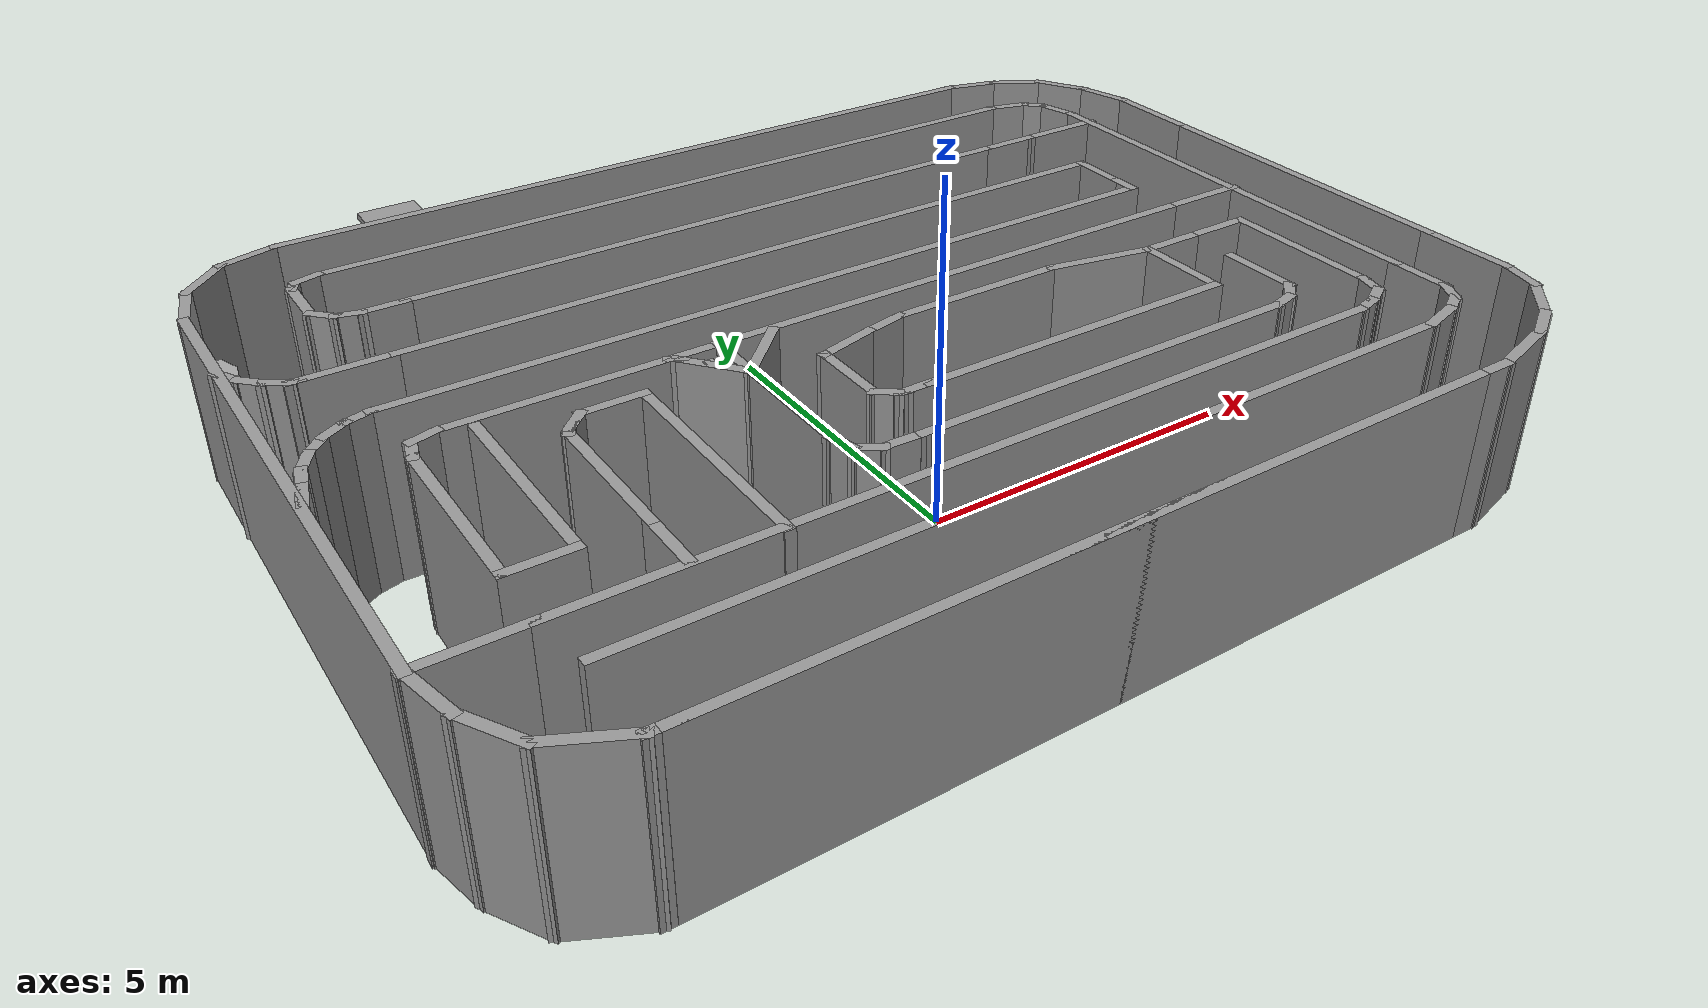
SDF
<?xml version='1.0'?>
<sdf version='1.7'>
  <model name='Race_Track'>
      <model name='Mailbox'>
      <link name='link'>
        <collision name='collision'>
          <geometry>
            <mesh>
              <uri>model://mailbox/meshes/mailbox.dae</uri>
            </mesh>
          </geometry>
        </collision>
        <visual name='visual'>
          <geometry>
            <mesh>
              <uri>model://mailbox/meshes/mailbox.dae</uri>
            </mesh>
          </geometry>
          <material>
            <script>
              <uri>model://mailbox/materials/scripts</uri>
              <uri>model://mailbox/materials/textures</uri>
              <name>Mailbox/Diffuse</name>
            </script>
          </material>
        </visual>
      </link>
      <pose>7.00567 3.1842 -0.178331 0 -0 0</pose>
    </model>
    <model name='Stop Sign'>
      <static>1</static>
      <link name='link'>
        <collision name='collision'>
          <geometry>
            <mesh>
              <uri>model://stop_sign/meshes/stop_sign.dae</uri>
            </mesh>
          </geometry>
        </collision>
        <visual name='visual'>
          <geometry>
            <mesh>
              <uri>model://stop_sign/meshes/stop_sign.dae</uri>
            </mesh>
          </geometry>
          <material>
            <script>
              <uri>model://stop_sign/materials/scripts</uri>
              <uri>model://stop_sign/materials/textures</uri>
              <name>StopSign/Diffuse</name>
            </script>
          </material>
        </visual>
      </link>
      <pose>-7.69841 4.6734 -0.178331 0 -0 3.13707</pose>
    </model>
    <model name='bookshelf'>
      <static>1</static>
      <link name='link'>
        <inertial>
          <mass>1</mass>
        </inertial>
        <collision name='back'>
          <pose>0 0.005 0.6 0 -0 0</pose>
          <geometry>
            <box>
              <size>0.9 0.01 1.2</size>
            </box>
          </geometry>
        </collision>
        <visual name='visual1'>
          <pose>0 0.005 0.6 0 -0 0</pose>
          <geometry>
            <box>
              <size>0.9 0.01 1.2</size>
            </box>
          </geometry>
          <material>
            <script>
              <uri>file://media/materials/scripts/gazebo.material</uri>
              <name>Gazebo/Wood</name>
            </script>
          </material>
        </visual>
        <collision name='left_side'>
          <pose>0.45 -0.195 0.6 0 -0 0</pose>
          <geometry>
            <box>
              <size>0.02 0.4 1.2</size>
            </box>
          </geometry>
        </collision>
        <visual name='visual2'>
          <pose>0.45 -0.195 0.6 0 -0 0</pose>
          <geometry>
            <box>
              <size>0.02 0.4 1.2</size>
            </box>
          </geometry>
          <material>
            <script>
              <uri>file://media/materials/scripts/gazebo.material</uri>
              <name>Gazebo/Wood</name>
            </script>
          </material>
        </visual>
        <collision name='right_side'>
          <pose>-0.45 -0.195 0.6 0 -0 0</pose>
          <geometry>
            <box>
              <size>0.02 0.4 1.2</size>
            </box>
          </geometry>
        </collision>
        <visual name='visual3'>
          <pose>-0.45 -0.195 0.6 0 -0 0</pose>
          <geometry>
            <box>
              <size>0.02 0.4 1.2</size>
            </box>
          </geometry>
          <material>
            <script>
              <uri>file://media/materials/scripts/gazebo.material</uri>
              <name>Gazebo/Wood</name>
            </script>
          </material>
        </visual>
        <collision name='bottom'>
          <pose>0 -0.195 0.03 0 -0 0</pose>
          <geometry>
            <box>
              <size>0.88 0.4 0.06</size>
            </box>
          </geometry>
        </collision>
        <visual name='visual4'>
          <pose>0 -0.195 0.03 0 -0 0</pose>
          <geometry>
            <box>
              <size>0.88 0.4 0.06</size>
            </box>
          </geometry>
          <material>
            <script>
              <uri>file://media/materials/scripts/gazebo.material</uri>
              <name>Gazebo/Wood</name>
            </script>
          </material>
        </visual>
        <collision name='top'>
          <pose>0 -0.195 1.19 0 -0 0</pose>
          <geometry>
            <box>
              <size>0.88 0.4 0.02</size>
            </box>
          </geometry>
        </collision>
        <visual name='visual5'>
          <pose>0 -0.195 1.19 0 -0 0</pose>
          <geometry>
            <box>
              <size>0.88 0.4 0.02</size>
            </box>
          </geometry>
          <material>
            <script>
              <uri>file://media/materials/scripts/gazebo.material</uri>
              <name>Gazebo/Wood</name>
            </script>
          </material>
        </visual>
        <collision name='low_shelf'>
          <pose>0 -0.195 0.43 0 -0 0</pose>
          <geometry>
            <box>
              <size>0.88 0.4 0.02</size>
            </box>
          </geometry>
        </collision>
        <visual name='visual6'>
          <pose>0 -0.195 0.43 0 -0 0</pose>
          <geometry>
            <box>
              <size>0.88 0.4 0.02</size>
            </box>
          </geometry>
          <material>
            <script>
              <uri>file://media/materials/scripts/gazebo.material</uri>
              <name>Gazebo/Wood</name>
            </script>
          </material>
        </visual>
        <collision name='high_shelf'>
          <pose>0 -0.195 0.8 0 -0 0</pose>
          <geometry>
            <box>
              <size>0.88 0.4 0.02</size>
            </box>
          </geometry>
        </collision>
        <visual name='visual7'>
          <pose>0 -0.195 0.8 0 -0 0</pose>
          <geometry>
            <box>
              <size>0.88 0.4 0.02</size>
            </box>
          </geometry>
          <material>
            <script>
              <uri>file://media/materials/scripts/gazebo.material</uri>
              <name>Gazebo/Wood</name>
            </script>
          </material>
        </visual>
      </link>
      <pose>-1.7139 -4.20805 -0.178331 0 -0 0</pose>
    </model>
    <model name='bookshelf_0'>
      <static>1</static>
      <link name='link'>
        <inertial>
          <mass>1</mass>
        </inertial>
        <collision name='back'>
          <pose>0 0.005 0.6 0 -0 0</pose>
          <geometry>
            <box>
              <size>0.9 0.01 1.2</size>
            </box>
          </geometry>
        </collision>
        <visual name='visual1'>
          <pose>0 0.005 0.6 0 -0 0</pose>
          <geometry>
            <box>
              <size>0.9 0.01 1.2</size>
            </box>
          </geometry>
          <material>
            <script>
              <uri>file://media/materials/scripts/gazebo.material</uri>
              <name>Gazebo/Wood</name>
            </script>
          </material>
        </visual>
        <collision name='left_side'>
          <pose>0.45 -0.195 0.6 0 -0 0</pose>
          <geometry>
            <box>
              <size>0.02 0.4 1.2</size>
            </box>
          </geometry>
        </collision>
        <visual name='visual2'>
          <pose>0.45 -0.195 0.6 0 -0 0</pose>
          <geometry>
            <box>
              <size>0.02 0.4 1.2</size>
            </box>
          </geometry>
          <material>
            <script>
              <uri>file://media/materials/scripts/gazebo.material</uri>
              <name>Gazebo/Wood</name>
            </script>
          </material>
        </visual>
        <collision name='right_side'>
          <pose>-0.45 -0.195 0.6 0 -0 0</pose>
          <geometry>
            <box>
              <size>0.02 0.4 1.2</size>
            </box>
          </geometry>
        </collision>
        <visual name='visual3'>
          <pose>-0.45 -0.195 0.6 0 -0 0</pose>
          <geometry>
            <box>
              <size>0.02 0.4 1.2</size>
            </box>
          </geometry>
          <material>
            <script>
              <uri>file://media/materials/scripts/gazebo.material</uri>
              <name>Gazebo/Wood</name>
            </script>
          </material>
        </visual>
        <collision name='bottom'>
          <pose>0 -0.195 0.03 0 -0 0</pose>
          <geometry>
            <box>
              <size>0.88 0.4 0.06</size>
            </box>
          </geometry>
        </collision>
        <visual name='visual4'>
          <pose>0 -0.195 0.03 0 -0 0</pose>
          <geometry>
            <box>
              <size>0.88 0.4 0.06</size>
            </box>
          </geometry>
          <material>
            <script>
              <uri>file://media/materials/scripts/gazebo.material</uri>
              <name>Gazebo/Wood</name>
            </script>
          </material>
        </visual>
        <collision name='top'>
          <pose>0 -0.195 1.19 0 -0 0</pose>
          <geometry>
            <box>
              <size>0.88 0.4 0.02</size>
            </box>
          </geometry>
        </collision>
        <visual name='visual5'>
          <pose>0 -0.195 1.19 0 -0 0</pose>
          <geometry>
            <box>
              <size>0.88 0.4 0.02</size>
            </box>
          </geometry>
          <material>
            <script>
              <uri>file://media/materials/scripts/gazebo.material</uri>
              <name>Gazebo/Wood</name>
            </script>
          </material>
        </visual>
        <collision name='low_shelf'>
          <pose>0 -0.195 0.43 0 -0 0</pose>
          <geometry>
            <box>
              <size>0.88 0.4 0.02</size>
            </box>
          </geometry>
        </collision>
        <visual name='visual6'>
          <pose>0 -0.195 0.43 0 -0 0</pose>
          <geometry>
            <box>
              <size>0.88 0.4 0.02</size>
            </box>
          </geometry>
          <material>
            <script>
              <uri>file://media/materials/scripts/gazebo.material</uri>
              <name>Gazebo/Wood</name>
            </script>
          </material>
        </visual>
        <collision name='high_shelf'>
          <pose>0 -0.195 0.8 0 -0 0</pose>
          <geometry>
            <box>
              <size>0.88 0.4 0.02</size>
            </box>
          </geometry>
        </collision>
        <visual name='visual7'>
          <pose>0 -0.195 0.8 0 -0 0</pose>
          <geometry>
            <box>
              <size>0.88 0.4 0.02</size>
            </box>
          </geometry>
          <material>
            <script>
              <uri>file://media/materials/scripts/gazebo.material</uri>
              <name>Gazebo/Wood</name>
            </script>
          </material>
        </visual>
      </link>
      <pose>2.63462 -4.96152 -0.178331 0 -0 0</pose>
    </model>
    <model name='fire_hydrant'>
      <static>1</static>
      <link name='link'>
        <collision name='collision'>
          <geometry>
            <mesh>
              <uri>model://fire_hydrant/meshes/fire_hydrant.dae</uri>
            </mesh>
          </geometry>
        </collision>
        <visual name='visual'>
          <geometry>
            <mesh>
              <uri>model://fire_hydrant/meshes/fire_hydrant.dae</uri>
            </mesh>
          </geometry>
        </visual>
      </link>
      <pose>7.33669 -2.30001 -0.178331 0 -0 0</pose>
    </model>
    <model name='fire_hydrant_0'>
      <static>1</static>
      <link name='link'>
        <collision name='collision'>
          <geometry>
            <mesh>
              <uri>model://fire_hydrant/meshes/fire_hydrant.dae</uri>
            </mesh>
          </geometry>
        </collision>
        <visual name='visual'>
          <geometry>
            <mesh>
              <uri>model://fire_hydrant/meshes/fire_hydrant.dae</uri>
            </mesh>
          </geometry>
        </visual>
      </link>
      <pose>7.38024 0.302282 -0.178331 0 -0 0</pose>
    </model>
    <model name='jersey_barrier'>
      <static>1</static>
      <link name='link'>
        <visual name='visual'>
          <geometry>
            <mesh>
              <uri>model://jersey_barrier/meshes/jersey_barrier.dae</uri>
            </mesh>
          </geometry>
        </visual>
        <collision name='upright'>
          <pose>0 0 0.5715 0 -0 0</pose>
          <geometry>
            <box>
              <size>4.06542 0.3063 1.143</size>
            </box>
          </geometry>
        </collision>
        <collision name='base'>
          <pose>0 0 0.032258 0 -0 0</pose>
          <geometry>
            <box>
              <size>4.06542 0.8107 0.064516</size>
            </box>
          </geometry>
        </collision>
        <collision name='base2'>
          <pose>0 0 0.1 0 -0 0</pose>
          <geometry>
            <box>
              <size>4.06542 0.65 0.1</size>
            </box>
          </geometry>
        </collision>
        <collision name='base3'>
          <pose>0 0 0.2 0 -0 0</pose>
          <geometry>
            <box>
              <size>4.06542 0.5 0.1</size>
            </box>
          </geometry>
        </collision>
        <collision name='left-angle'>
          <pose>0 -0.224 0.2401 0.9 -0 0</pose>
          <geometry>
            <box>
              <size>4.06542 0.5 0.064516</size>
            </box>
          </geometry>
        </collision>
        <collision name='right-angle'>
          <pose>0 0.224 0.2401 -0.9 0 0</pose>
          <geometry>
            <box>
              <size>4.06542 0.5 0.064516</size>
            </box>
          </geometry>
        </collision>
      </link>
      <pose>-1.18328 3.74123 -0.178331 0 -0 0</pose>
    </model>
    <model name='ladder_70deg_0rails'>
      <static>1</static>
      <link name='step0'>
        <pose>0 0.097059 0.266667 0 -0 0</pose>
        <inertial>
          <mass>9.75482</mass>
          <inertia>
            <ixx>0.00957124</ixx>
            <iyy>0.65963</iyy>
            <izz>0.666842</izz>
            <ixy>0</ixy>
            <ixz>0</ixz>
            <iyz>0</iyz>
          </inertia>
        </inertial>
        <collision name='collision'>
          <geometry>
            <box>
              <size>0.9 0.1016 0.0381</size>
            </box>
          </geometry>
        </collision>
        <visual name='visual'>
          <geometry>
            <box>
              <size>0.9 0.1016 0.0381</size>
            </box>
          </geometry>
          <material>
            <script>
              <uri>file://media/materials/scripts/gazebo.material</uri>
              <name>Gazebo/Grey</name>
            </script>
          </material>
        </visual>
      </link>
      <link name='step1'>
        <pose>0 0.194117 0.533333 0 -0 0</pose>
        <inertial>
          <mass>9.75482</mass>
          <inertia>
            <ixx>0.00957124</ixx>
            <iyy>0.65963</iyy>
            <izz>0.666842</izz>
            <ixy>0</ixy>
            <ixz>0</ixz>
            <iyz>0</iyz>
          </inertia>
        </inertial>
        <collision name='collision'>
          <geometry>
            <box>
              <size>0.9 0.1016 0.0381</size>
            </box>
          </geometry>
        </collision>
        <visual name='visual'>
          <geometry>
            <box>
              <size>0.9 0.1016 0.0381</size>
            </box>
          </geometry>
          <material>
            <script>
              <uri>file://media/materials/scripts/gazebo.material</uri>
              <name>Gazebo/Grey</name>
            </script>
          </material>
        </visual>
      </link>
      <link name='step2'>
        <pose>0 0.291176 0.8 0 -0 0</pose>
        <inertial>
          <mass>9.75482</mass>
          <inertia>
            <ixx>0.00957124</ixx>
            <iyy>0.65963</iyy>
            <izz>0.666842</izz>
            <ixy>0</ixy>
            <ixz>0</ixz>
            <iyz>0</iyz>
          </inertia>
        </inertial>
        <collision name='collision'>
          <geometry>
            <box>
              <size>0.9 0.1016 0.0381</size>
            </box>
          </geometry>
        </collision>
        <visual name='visual'>
          <geometry>
            <box>
              <size>0.9 0.1016 0.0381</size>
            </box>
          </geometry>
          <material>
            <script>
              <uri>file://media/materials/scripts/gazebo.material</uri>
              <name>Gazebo/Grey</name>
            </script>
          </material>
        </visual>
      </link>
      <link name='step3'>
        <pose>0 0.388235 1.06667 0 -0 0</pose>
        <inertial>
          <mass>9.75482</mass>
          <inertia>
            <ixx>0.00957124</ixx>
            <iyy>0.65963</iyy>
            <izz>0.666842</izz>
            <ixy>0</ixy>
            <ixz>0</ixz>
            <iyz>0</iyz>
          </inertia>
        </inertial>
        <collision name='collision'>
          <geometry>
            <box>
              <size>0.9 0.1016 0.0381</size>
            </box>
          </geometry>
        </collision>
        <visual name='visual'>
          <geometry>
            <box>
              <size>0.9 0.1016 0.0381</size>
            </box>
          </geometry>
          <material>
            <script>
              <uri>file://media/materials/scripts/gazebo.material</uri>
              <name>Gazebo/Grey</name>
            </script>
          </material>
        </visual>
      </link>
      <link name='step4'>
        <pose>0 0.485294 1.33333 0 -0 0</pose>
        <inertial>
          <mass>9.75482</mass>
          <inertia>
            <ixx>0.00957124</ixx>
            <iyy>0.65963</iyy>
            <izz>0.666842</izz>
            <ixy>0</ixy>
            <ixz>0</ixz>
            <iyz>0</iyz>
          </inertia>
        </inertial>
        <collision name='collision'>
          <geometry>
            <box>
              <size>0.9 0.1016 0.0381</size>
            </box>
          </geometry>
        </collision>
        <visual name='visual'>
          <geometry>
            <box>
              <size>0.9 0.1016 0.0381</size>
            </box>
          </geometry>
          <material>
            <script>
              <uri>file://media/materials/scripts/gazebo.material</uri>
              <name>Gazebo/Grey</name>
            </script>
          </material>
        </visual>
      </link>
      <link name='step5'>
        <pose>0 0.582352 1.6 0 -0 0</pose>
        <inertial>
          <mass>9.75482</mass>
          <inertia>
            <ixx>0.00957124</ixx>
            <iyy>0.65963</iyy>
            <izz>0.666842</izz>
            <ixy>0</ixy>
            <ixz>0</ixz>
            <iyz>0</iyz>
          </inertia>
        </inertial>
        <collision name='collision'>
          <geometry>
            <box>
              <size>0.9 0.1016 0.0381</size>
            </box>
          </geometry>
        </collision>
        <visual name='visual'>
          <geometry>
            <box>
              <size>0.9 0.1016 0.0381</size>
            </box>
          </geometry>
          <material>
            <script>
              <uri>file://media/materials/scripts/gazebo.material</uri>
              <name>Gazebo/Grey</name>
            </script>
          </material>
        </visual>
      </link>
      <link name='step6'>
        <pose>0 0.679411 1.86667 0 -0 0</pose>
        <inertial>
          <mass>9.75482</mass>
          <inertia>
            <ixx>0.00957124</ixx>
            <iyy>0.65963</iyy>
            <izz>0.666842</izz>
            <ixy>0</ixy>
            <ixz>0</ixz>
            <iyz>0</iyz>
          </inertia>
        </inertial>
        <collision name='collision'>
          <geometry>
            <box>
              <size>0.9 0.1016 0.0381</size>
            </box>
          </geometry>
        </collision>
        <visual name='visual'>
          <geometry>
            <box>
              <size>0.9 0.1016 0.0381</size>
            </box>
          </geometry>
          <material>
            <script>
              <uri>file://media/materials/scripts/gazebo.material</uri>
              <name>Gazebo/Grey</name>
            </script>
          </material>
        </visual>
      </link>
      <link name='step7'>
        <pose>0 0.77647 2.13333 0 -0 0</pose>
        <inertial>
          <mass>9.75482</mass>
          <inertia>
            <ixx>0.00957124</ixx>
            <iyy>0.65963</iyy>
            <izz>0.666842</izz>
            <ixy>0</ixy>
            <ixz>0</ixz>
            <iyz>0</iyz>
          </inertia>
        </inertial>
        <collision name='collision'>
          <geometry>
            <box>
              <size>0.9 0.1016 0.0381</size>
            </box>
          </geometry>
        </collision>
        <visual name='visual'>
          <geometry>
            <box>
              <size>0.9 0.1016 0.0381</size>
            </box>
          </geometry>
          <material>
            <script>
              <uri>file://media/materials/scripts/gazebo.material</uri>
              <name>Gazebo/Grey</name>
            </script>
          </material>
        </visual>
      </link>
      <link name='landing'>
        <pose>0 1.17353 2.4 0 -0 0</pose>
        <inertial>
          <mass>57.6072</mass>
          <inertia>
            <ixx>1.73518</ixx>
            <iyy>3.89545</iyy>
            <izz>5.6167</izz>
            <ixy>0</ixy>
            <ixz>0</ixz>
            <iyz>0</iyz>
          </inertia>
        </inertial>
        <collision name='collision'>
          <geometry>
            <box>
              <size>0.9 0.6 0.1016</size>
            </box>
          </geometry>
        </collision>
        <visual name='visual'>
          <geometry>
            <box>
              <size>0.9 0.6 0.1016</size>
            </box>
          </geometry>
          <material>
            <script>
              <uri>file://media/materials/scripts/gazebo.material</uri>
              <name>Gazebo/Grey</name>
            </script>
          </material>
        </visual>
      </link>
      <link name='left_side_wall'>
        <pose>-0.45 0.436764 1.2 1.22173 -0 0</pose>
        <collision name='collision'>
          <geometry>
            <box>
              <size>0.0508 2.63403 0.13</size>
            </box>
          </geometry>
        </collision>
        <visual name='visual'>
          <geometry>
            <box>
              <size>0.0508 2.63403 0.13</size>
            </box>
          </geometry>
          <material>
            <script>
              <uri>file://media/materials/scripts/gazebo.material</uri>
              <name>Gazebo/Grey</name>
            </script>
          </material>
        </visual>
      </link>
      <link name='right_side_wall'>
        <pose>0.45 0.436764 1.2 1.22173 -0 0</pose>
        <collision name='collision'>
          <geometry>
            <box>
              <size>0.0508 2.63403 0.13</size>
            </box>
          </geometry>
        </collision>
        <visual name='visual'>
          <geometry>
            <box>
              <size>0.0508 2.63403 0.13</size>
            </box>
          </geometry>
          <material>
            <script>
              <uri>file://media/materials/scripts/gazebo.material</uri>
              <name>Gazebo/Grey</name>
            </script>
          </material>
        </visual>
      </link>
      <pose>-4.38738 5.53394 -0.178331 0 -0 0</pose>
    </model>
    <model name='stop_light'>
      <static>1</static>
      <pose>-5.54624 -4.30489 1.60498 0 -0 0</pose>
      <link name='link'>
        <collision name='collision'>
          <geometry>
            <mesh>
              <uri>model://stop_light/meshes/stop_light.obj</uri>
              <scale>0.01 0.01 0.01</scale>
            </mesh>
          </geometry>
        </collision>
        <visual name='frame'>
          <geometry>
            <mesh>
              <uri>model://stop_light/meshes/stop_light.obj</uri>
              <scale>0.01 0.01 0.01</scale>
            </mesh>
          </geometry>
        </visual>
        <visual name='red'>
          <pose>-0.001123 -0.082251 -0.147514 0 -0 0</pose>
          <geometry>
            <sphere>
              <radius>0.1012</radius>
            </sphere>
          </geometry>
          <material>
            <script>
              <uri>model://stop_light/materials/scripts/</uri>
              <uri>model://stop_light/materials/textures/</uri>
              <name>StopLight/Light</name>
            </script>
            <ambient>1 0 0 1</ambient>
            <specular>1 0 0 1</specular>
          </material>
        </visual>
        <visual name='yellow'>
          <pose>-0.001123 -0.082251 -0.402 0 -0 0</pose>
          <geometry>
            <sphere>
              <radius>0.1012</radius>
            </sphere>
          </geometry>
          <material>
            <script>
              <uri>model://stop_light/materials/scripts/</uri>
              <uri>model://stop_light/materials/textures/</uri>
              <name>StopLight/Light</name>
            </script>
            <ambient>1 1 0 1</ambient>
            <specular>1 1 0 1</specular>
          </material>
        </visual>
        <visual name='green'>
          <pose>-0.001123 -0.082251 -0.655 0 -0 0</pose>
          <geometry>
            <sphere>
              <radius>0.1012</radius>
            </sphere>
          </geometry>
          <material>
            <script>
              <uri>model://stop_light/materials/scripts/</uri>
              <uri>model://stop_light/materials/textures/</uri>
              <name>StopLight/Light</name>
            </script>
            <ambient>0 1 0 1</ambient>
            <specular>0 1 0 1</specular>
          </material>
        </visual>
      </link>
    </model>
    <model name='turtlebot'>
      <link name='rack'>
        <inertial>
          <pose>0.001453 -0.000453 0.029787 0 -0 0</pose>
          <inertia>
            <ixx>0.05864</ixx>
            <ixy>0.000124</ixy>
            <ixz>0.000615</ixz>
            <iyy>0.058786</iyy>
            <iyz>1.4e-05</iyz>
            <izz>1.53244</izz>
          </inertia>
          <mass>2.234</mass>
        </inertial>
        <collision name='plate_0_collision'>
          <pose>-0.04334 0 0.084757 0 -0 0</pose>
          <geometry>
            <box>
              <size>0.233502 0.314845 0.006401</size>
            </box>
          </geometry>
        </collision>
        <visual name='plate_0_visual'>
          <pose>-0.04334 0 0.084757 0 -0 0</pose>
          <geometry>
            <mesh>
              <uri>model://turtlebot/meshes/plate_0_logo.dae</uri>
            </mesh>
          </geometry>
        </visual>
        <collision name='plate_1_collision'>
          <pose>-0.00266 0 0.141907 0 -0 0</pose>
          <geometry>
            <box>
              <size>0.314856 0.314856 0.006401</size>
            </box>
          </geometry>
        </collision>
        <visual name='plate_1_visual'>
          <pose>-0.00266 0 0.141907 0 -0 0</pose>
          <geometry>
            <mesh>
              <uri>model://turtlebot/meshes/plate_1_logo.dae</uri>
            </mesh>
          </geometry>
        </visual>
        <collision name='plate_2_collision'>
          <pose>-0.00266 0 0.199108 0 -0 0</pose>
          <geometry>
            <box>
              <size>0.314856 0.314856 0.006401</size>
            </box>
          </geometry>
        </collision>
        <visual name='plate_2_visual'>
          <pose>-0.00266 0 0.199108 0 -0 0</pose>
          <geometry>
            <mesh>
              <uri>model://turtlebot/meshes/plate_1_logo.dae</uri>
            </mesh>
          </geometry>
        </visual>
        <collision name='plate_3_collision'>
          <pose>-0.01582 0 0.405457 0 -0 0</pose>
          <geometry>
            <box>
              <size>0.288 0.315 0.006401</size>
            </box>
          </geometry>
        </collision>
        <visual name='plate_3_visual'>
          <pose>-0.01582 0 0.405457 0 -0 0</pose>
          <geometry>
            <mesh>
              <uri>model://turtlebot/meshes/plate_2_logo.dae</uri>
            </mesh>
          </geometry>
        </visual>
        <collision name='spacer_0_collision'>
          <pose>-0.00254 0.111468 0.079992 0 -0 0</pose>
          <geometry>
            <cylinder>
              <radius>0.0127</radius>
              <length>0.003175</length>
            </cylinder>
          </geometry>
        </collision>
        <visual name='spacer_0_visual'>
          <pose>-0.00254 0.111468 0.079992 0 -0 0</pose>
          <geometry>
            <mesh>
              <uri>model://turtlebot/meshes/68-02403-125_Spacer.dae</uri>
            </mesh>
          </geometry>
        </visual>
        <collision name='spacer_1_collision'>
          <pose>-0.00254 -0.111468 0.079992 0 -0 0</pose>
          <geometry>
            <cylinder>
              <radius>0.0127</radius>
              <length>0.003175</length>
            </cylinder>
          </geometry>
        </collision>
        <visual name='spacer_1_visual'>
          <pose>-0.00254 -0.111468 0.079992 0 -0 0</pose>
          <geometry>
            <mesh>
              <uri>model://turtlebot/meshes/68-02403-125_Spacer.dae</uri>
            </mesh>
          </geometry>
        </visual>
        <collision name='spacer_2_collision'>
          <pose>-0.07239 -0.111468 0.079992 0 -0 0</pose>
          <geometry>
            <cylinder>
              <radius>0.0127</radius>
              <length>0.003175</length>
            </cylinder>
          </geometry>
        </collision>
        <visual name='spacer_2_visual'>
          <pose>-0.07239 -0.111468 0.079992 0 -0 0</pose>
          <geometry>
            <mesh>
              <uri>model://turtlebot/meshes/68-02403-125_Spacer.dae</uri>
            </mesh>
          </geometry>
        </visual>
        <collision name='spacer_3_collision'>
          <pose>-0.07239 0.111468 0.079992 0 -0 0</pose>
          <geometry>
            <cylinder>
              <radius>0.0127</radius>
              <length>0.003175</length>
            </cylinder>
          </geometry>
        </collision>
        <visual name='spacer_3_visual'>
          <pose>-0.07239 0.111468 0.079992 0 -0 0</pose>
          <geometry>
            <mesh>
              <uri>model://turtlebot/meshes/68-02403-125_Spacer.dae</uri>
            </mesh>
          </geometry>
        </visual>
        <collision name='standoff_2in_0_collision'>
          <pose>0.06764 0.13142 0.08798 0 -0 0</pose>
          <geometry>
            <cylinder>
              <radius>0.0381</radius>
              <length>0.0635</length>
            </cylinder>
          </geometry>
        </collision>
        <visual name='standoff_2in_0_visual'>
          <pose>0.06764 0.13142 0.08798 0 -0 0</pose>
          <geometry>
            <mesh>
              <uri>model://turtlebot/meshes/68-04552-2000-RA_Turtlebot_M-F_Standoff.dae</uri>
            </mesh>
          </geometry>
        </visual>
        <collision name='standoff_2in_1_collision'>
          <pose>0.06764 -0.13142 0.08798 0 -0 0</pose>
          <geometry>
            <cylinder>
              <radius>0.0381</radius>
              <length>0.0635</length>
            </cylinder>
          </geometry>
        </collision>
        <visual name='standoff_2in_1_visual'>
          <pose>0.06764 -0.13142 0.08798 0 -0 0</pose>
          <geometry>
            <mesh>
              <uri>model://turtlebot/meshes/68-04552-2000-RA_Turtlebot_M-F_Standoff.dae</uri>
            </mesh>
          </geometry>
        </visual>
        <collision name='standoff_2in_2_collision'>
          <pose>-0.052832 -0.13142 0.08798 0 -0 0</pose>
          <geometry>
            <cylinder>
              <radius>0.0381</radius>
              <length>0.0635</length>
            </cylinder>
          </geometry>
        </collision>
        <visual name='standoff_2in_2_visual'>
          <pose>-0.052832 -0.13142 0.08798 0 -0 0</pose>
          <geometry>
            <mesh>
              <uri>model://turtlebot/meshes/68-04552-2000-RA_Turtlebot_M-F_Standoff.dae</uri>
            </mesh>
          </geometry>
        </visual>
        <collision name='standoff_2in_3_collision'>
          <pose>-0.052832 0.13142 0.08798 0 -0 0</pose>
          <geometry>
            <cylinder>
              <radius>0.0381</radius>
              <length>0.0635</length>
            </cylinder>
          </geometry>
        </collision>
        <visual name='standoff_2in_3_visual'>
          <pose>-0.052832 0.13142 0.08798 0 -0 0</pose>
          <geometry>
            <mesh>
              <uri>model://turtlebot/meshes/68-04552-2000-RA_Turtlebot_M-F_Standoff.dae</uri>
            </mesh>
          </geometry>
        </visual>
        <collision name='standoff_2in_4_collision'>
          <pose>0.06764 0.13142 0.14513 0 -0 0</pose>
          <geometry>
            <cylinder>
              <radius>0.0381</radius>
              <length>0.0635</length>
            </cylinder>
          </geometry>
        </collision>
        <visual name='standoff_2in_4_visual'>
          <pose>0.06764 0.13142 0.14513 0 -0 0</pose>
          <geometry>
            <mesh>
              <uri>model://turtlebot/meshes/68-04552-2000-RA_Turtlebot_M-F_Standoff.dae</uri>
            </mesh>
          </geometry>
        </visual>
        <collision name='standoff_2in_5_collision'>
          <pose>0.06764 -0.13142 0.14513 0 -0 0</pose>
          <geometry>
            <cylinder>
              <radius>0.0381</radius>
              <length>0.0635</length>
            </cylinder>
          </geometry>
        </collision>
        <visual name='standoff_2in_5_visual'>
          <pose>0.06764 -0.13142 0.14513 0 -0 0</pose>
          <geometry>
            <mesh>
              <uri>model://turtlebot/meshes/68-04552-2000-RA_Turtlebot_M-F_Standoff.dae</uri>
            </mesh>
          </geometry>
        </visual>
        <collision name='standoff_2in_6_collision'>
          <pose>-0.052832 -0.13142 0.14513 0 -0 0</pose>
          <geometry>
            <cylinder>
              <radius>0.0381</radius>
              <length>0.0635</length>
            </cylinder>
          </geometry>
        </collision>
        <visual name='standoff_2in_6_visual'>
          <pose>-0.052832 -0.13142 0.14513 0 -0 0</pose>
          <geometry>
            <mesh>
              <uri>model://turtlebot/meshes/68-04552-2000-RA_Turtlebot_M-F_Standoff.dae</uri>
            </mesh>
          </geometry>
        </visual>
        <collision name='standoff_2in_7_collision'>
          <pose>-0.052832 0.13142 0.14513 0 -0 0</pose>
          <geometry>
            <cylinder>
              <radius>0.0381</radius>
              <length>0.0635</length>
            </cylinder>
          </geometry>
        </collision>
        <visual name='standoff_2in_7_visual'>
          <pose>-0.052832 0.13142 0.14513 0 -0 0</pose>
          <geometry>
            <mesh>
              <uri>model://turtlebot/meshes/68-04552-2000-RA_Turtlebot_M-F_Standoff.dae</uri>
            </mesh>
          </geometry>
        </visual>
        <collision name='standoff_8in_0_collision'>
          <pose>0.06764 0.13142 0.20228 0 -0 0</pose>
          <geometry>
            <cylinder>
              <radius>0.011113</radius>
              <length>0.2032</length>
            </cylinder>
          </geometry>
        </collision>
        <visual name='standoff_8in_0_visual'>
          <pose>0.06764 0.13142 0.20228 0 -0 0</pose>
          <geometry>
            <mesh>
              <uri>model://turtlebot/meshes/68-02421-8000-RA_Turtlebot_F-F_Standoff.dae</uri>
            </mesh>
          </geometry>
        </visual>
        <collision name='standoff_8in_1_collision'>
          <pose>0.06764 -0.13142 0.20228 0 -0 0</pose>
          <geometry>
            <cylinder>
              <radius>0.011113</radius>
              <length>0.2032</length>
            </cylinder>
          </geometry>
        </collision>
        <visual name='standoff_8in_1_visual'>
          <pose>0.06764 -0.13142 0.20228 0 -0 0</pose>
          <geometry>
            <mesh>
              <uri>model://turtlebot/meshes/68-02421-8000-RA_Turtlebot_F-F_Standoff.dae</uri>
            </mesh>
          </geometry>
        </visual>
        <collision name='standoff_8in_2_collision'>
          <pose>-0.052832 -0.13142 0.20228 0 -0 0</pose>
          <geometry>
            <cylinder>
              <radius>0.011113</radius>
              <length>0.2032</length>
            </cylinder>
          </geometry>
        </collision>
        <visual name='standoff_8in_2_visual'>
          <pose>-0.052832 -0.13142 0.20228 0 -0 0</pose>
          <geometry>
            <mesh>
              <uri>model://turtlebot/meshes/68-02421-8000-RA_Turtlebot_F-F_Standoff.dae</uri>
            </mesh>
          </geometry>
        </visual>
        <collision name='standoff_8in_3_collision'>
          <pose>-0.052832 0.13142 0.20228 0 -0 0</pose>
          <geometry>
            <cylinder>
              <radius>0.011113</radius>
              <length>0.2032</length>
            </cylinder>
          </geometry>
        </collision>
        <visual name='standoff_8in_3_visual'>
          <pose>-0.052832 0.13142 0.20228 0 -0 0</pose>
          <geometry>
            <mesh>
              <uri>model://turtlebot/meshes/68-02421-8000-RA_Turtlebot_F-F_Standoff.dae</uri>
            </mesh>
          </geometry>
        </visual>
        <collision name='standoff_kinect_0_collision'>
          <pose>-0.105098 0.098 0.202308 0 -0 0</pose>
          <geometry>
            <cylinder>
              <radius>0.001111</radius>
              <length>0.008585</length>
            </cylinder>
          </geometry>
        </collision>
        <visual name='standoff_kinect_0_visual'>
          <pose>-0.105098 0.098 0.202308 0 -0 0</pose>
          <geometry>
            <mesh>
              <uri>model://turtlebot/meshes/68-04556-RA_Kinect_Standoff_Assy.dae</uri>
            </mesh>
          </geometry>
        </visual>
        <collision name='standoff_kinect_1_collision'>
          <pose>-0.105098 -0.098 0.202308 0 -0 0</pose>
          <geometry>
            <cylinder>
              <radius>0.001111</radius>
              <length>0.008585</length>
            </cylinder>
          </geometry>
        </collision>
        <visual name='standoff_kinect_1_visual'>
          <pose>-0.105098 -0.098 0.202308 0 -0 0</pose>
          <geometry>
            <mesh>
              <uri>model://turtlebot/meshes/68-04556-RA_Kinect_Standoff_Assy.dae</uri>
            </mesh>
          </geometry>
        </visual>
        <sensor name='laser' type='ray'>
          <pose>-0.065 0 0.092 0 -0 0</pose>
          <ray>
            <scan>
              <horizontal>
                <samples>180</samples>
                <resolution>1</resolution>
                <min_angle>-2.26893</min_angle>
                <max_angle>2.26893</max_angle>
              </horizontal>
            </scan>
            <range>
              <min>0.08</min>
              <max>10</max>
              <resolution>0.01</resolution>
            </range>
          </ray>
          <update_rate>20</update_rate>
        </sensor>
      </link>
      <frame name='create::__model__' attached_to='create::base'>
        <pose relative_to='__model__'>0 0 0 0 -0 0</pose>
      </frame>
      <link name='create::base'>
        <inertial>
          <pose>0.001453 -0.000453 0.029787 0 -0 0</pose>
          <inertia>
            <ixx>0.05864</ixx>
            <ixy>0.000124</ixy>
            <ixz>0.000615</ixz>
            <iyy>0.058786</iyy>
            <iyz>1.4e-05</iyz>
            <izz>1.53244</izz>
          </inertia>
          <mass>2.234</mass>
        </inertial>
        <collision name='base_collision'>
          <pose>0 0 0.0478 0 -0 0</pose>
          <geometry>
            <cylinder>
              <radius>0.016495</radius>
              <length>0.061163</length>
            </cylinder>
          </geometry>
        </collision>
        <visual name='base_visual'>
          <pose>0 0 0.0478 0 -0 0</pose>
          <geometry>
            <mesh>
              <uri>model://create/meshes/create_body.dae</uri>
            </mesh>
          </geometry>
        </visual>
        <collision name='front_wheel_collision'>
          <pose>0.13 0 0.017 -0 1.5707 1.5707</pose>
          <geometry>
            <sphere>
              <radius>0.018</radius>
            </sphere>
          </geometry>
          <surface>
            <friction>
              <ode>
                <mu>0</mu>
                <mu2>0</mu2>
                <fdir1>0 0 0</fdir1>
                <slip1>0</slip1>
                <slip2>0</slip2>
              </ode>
            </friction>
          </surface>
        </collision>
        <visual name='front_wheel_visual'>
          <pose>0.13 0 0.017 -0 1.5707 1.5707</pose>
          <geometry>
            <sphere>
              <radius>0.009</radius>
            </sphere>
          </geometry>
        </visual>
        <collision name='rear_wheel_collision'>
          <pose>-0.13 0 0.017 -0 1.5707 1.5707</pose>
          <geometry>
            <sphere>
              <radius>0.015</radius>
            </sphere>
          </geometry>
          <surface>
            <friction>
              <ode>
                <mu>0</mu>
                <mu2>0</mu2>
                <fdir1>0 0 0</fdir1>
                <slip1>0</slip1>
                <slip2>0</slip2>
              </ode>
            </friction>
          </surface>
        </collision>
        <visual name='rear_wheel_visual'>
          <pose>-0.13 0 0.017 -0 1.5707 1.5707</pose>
          <geometry>
            <sphere>
              <radius>0.0075</radius>
            </sphere>
          </geometry>
        </visual>
        <sensor name='left_cliff_sensor' type='ray'>
          <pose>0.07 0.14 0.027 0 1.57079 0</pose>
          <ray>
            <scan>
              <horizontal>
                <samples>1</samples>
                <resolution>1</resolution>
                <min_angle>0</min_angle>
                <max_angle>0</max_angle>
              </horizontal>
            </scan>
            <range>
              <min>0.01</min>
              <max>0.04</max>
              <resolution>0.1</resolution>
            </range>
          </ray>
        </sensor>
        <sensor name='leftfront_cliff_sensor' type='ray'>
          <pose>0.15 0.04 0.027 0 1.57079 0</pose>
          <ray>
            <scan>
              <horizontal>
                <samples>1</samples>
                <resolution>1</resolution>
                <min_angle>0</min_angle>
                <max_angle>0</max_angle>
              </horizontal>
            </scan>
            <range>
              <min>0.01</min>
              <max>0.04</max>
              <resolution>0.1</resolution>
            </range>
          </ray>
        </sensor>
        <sensor name='right_cliff_sensor' type='ray'>
          <pose>0.07 -0.14 0.027 0 1.57079 0</pose>
          <ray>
            <scan>
              <horizontal>
                <samples>1</samples>
                <resolution>1</resolution>
                <min_angle>0</min_angle>
                <max_angle>0</max_angle>
              </horizontal>
            </scan>
            <range>
              <min>0.01</min>
              <max>0.04</max>
              <resolution>0.1</resolution>
            </range>
          </ray>
        </sensor>
        <sensor name='rightfront_cliff_sensor' type='ray'>
          <pose>0.15 -0.04 0.027 0 1.57079 0</pose>
          <ray>
            <scan>
              <horizontal>
                <samples>1</samples>
                <resolution>1</resolution>
                <min_angle>0</min_angle>
                <max_angle>0</max_angle>
              </horizontal>
            </scan>
            <range>
              <min>0.01</min>
              <max>0.04</max>
              <resolution>0.1</resolution>
            </range>
          </ray>
        </sensor>
        <sensor name='wall_sensor' type='ray'>
          <pose>0.09 -0.12 0.059 0 0 -1</pose>
          <ray>
            <scan>
              <horizontal>
                <samples>1</samples>
                <resolution>1</resolution>
                <min_angle>0</min_angle>
                <max_angle>0</max_angle>
              </horizontal>
            </scan>
            <range>
              <min>0.016</min>
              <max>0.04</max>
              <resolution>0.1</resolution>
            </range>
          </ray>
        </sensor>
        <pose>0 0 0 0 -0 0</pose>
      </link>
      <link name='create::left_wheel'>
        <pose>0 0.13 0.032 0 -0 0</pose>
        <inertial>
          <inertia>
            <ixx>0.001</ixx>
            <ixy>0</ixy>
            <ixz>0</ixz>
            <iyy>0.001</iyy>
            <iyz>0</iyz>
            <izz>0.001</izz>
          </inertia>
          <mass>0.01</mass>
        </inertial>
        <collision name='collision'>
          <pose>0 0 0 -0 1.5707 1.5707</pose>
          <geometry>
            <cylinder>
              <radius>0.033</radius>
              <length>0.023</length>
            </cylinder>
          </geometry>
          <surface>
            <friction>
              <ode>
                <mu>10</mu>
                <mu2>10</mu2>
                <fdir1>0 0 0</fdir1>
                <slip1>0</slip1>
                <slip2>0</slip2>
              </ode>
            </friction>
          </surface>
        </collision>
        <visual name='visual'>
          <pose>0 0 0 -0 1.5707 1.5707</pose>
          <geometry>
            <cylinder>
              <radius>0.033</radius>
              <length>0.023</length>
            </cylinder>
          </geometry>
        </visual>
      </link>
      <link name='create::right_wheel'>
        <pose>0 -0.13 0.032 0 -0 0</pose>
        <inertial>
          <inertia>
            <ixx>0.001</ixx>
            <ixy>0</ixy>
            <ixz>0</ixz>
            <iyy>0.001</iyy>
            <iyz>0</iyz>
            <izz>0.001</izz>
          </inertia>
          <mass>0.01</mass>
        </inertial>
        <collision name='collision'>
          <pose>0 0 0 -0 1.5707 1.5707</pose>
          <geometry>
            <cylinder>
              <radius>0.033</radius>
              <length>0.023</length>
            </cylinder>
          </geometry>
          <surface>
            <friction>
              <ode>
                <mu>10</mu>
                <mu2>10</mu2>
                <fdir1>0 0 0</fdir1>
                <slip1>0</slip1>
                <slip2>0</slip2>
              </ode>
            </friction>
          </surface>
        </collision>
        <visual name='visual'>
          <pose>0 0 0 -0 1.5707 1.5707</pose>
          <geometry>
            <cylinder>
              <radius>0.033</radius>
              <length>0.023</length>
            </cylinder>
          </geometry>
        </visual>
      </link>
      <joint name='create::left_wheel' type='revolute'>
        <parent>create::base</parent>
        <child>create::left_wheel</child>
        <axis>
          <xyz>0 1 0</xyz>
          <limit>
            <lower>-1e+16</lower>
            <upper>1e+16</upper>
          </limit>
        </axis>
      </joint>
      <joint name='create::right_wheel' type='revolute'>
        <parent>create::base</parent>
        <child>create::right_wheel</child>
        <axis>
          <xyz>0 1 0</xyz>
          <limit>
            <lower>-1e+16</lower>
            <upper>1e+16</upper>
          </limit>
        </axis>
      </joint>
      <frame name='kinect::__model__' attached_to='kinect::link'>
        <pose relative_to='__model__'>-0.087098 0 0.303857 0 -0 0</pose>
      </frame>
      <link name='kinect::link'>
        <inertial>
          <mass>0.1</mass>
        </inertial>
        <collision name='collision'>
          <geometry>
            <box>
              <size>0.073 0.276 0.072</size>
            </box>
          </geometry>
        </collision>
        <visual name='visual'>
          <geometry>
            <mesh>
              <uri>model://kinect/meshes/kinect.dae</uri>
            </mesh>
          </geometry>
        </visual>
        <sensor name='camera' type='depth'>
          <update_rate>20</update_rate>
          <camera>
            <horizontal_fov>1.0472</horizontal_fov>
            <image>
              <width>640</width>
              <height>480</height>
              <format>R8G8B8</format>
            </image>
            <clip>
              <near>0.05</near>
              <far>3</far>
            </clip>
          </camera>
        </sensor>
        <pose>-0.087098 0 0.303857 0 -0 0</pose>
      </link>
      <joint name='create_rack' type='revolute'>
        <parent>create::base</parent>
        <child>rack</child>
        <axis>
          <xyz expressed_in='__model__'>0 0 1</xyz>
          <limit>
            <lower>0</lower>
            <upper>0</upper>
          </limit>
        </axis>
      </joint>
      <joint name='kinect_rack' type='revolute'>
        <parent>kinect::link</parent>
        <child>rack</child>
        <axis>
          <xyz expressed_in='__model__'>0 0 1</xyz>
          <limit>
            <lower>0</lower>
            <upper>0</upper>
          </limit>
        </axis>
      </joint>
      <pose>-3.82802 -1.66057 -0.178331 0 -0 0</pose>
    </model>
    <pose>0.260432 2.01796 0 0 -0 0</pose>
    <link name='Wall_0'>
      <collision name='Wall_0_Collision'>
        <geometry>
          <box>
            <size>6.25 0.15 2.5</size>
          </box>
        </geometry>
        <pose>0 0 1.25 0 -0 0</pose>
      </collision>
      <visual name='Wall_0_Visual'>
        <pose>0 0 1.25 0 -0 0</pose>
        <geometry>
          <box>
            <size>6.25 0.15 2.5</size>
          </box>
        </geometry>
        <material>
          <script>
            <uri>file://media/materials/scripts/gazebo.material</uri>
            <name>Gazebo/Grey</name>
          </script>
          <ambient>1 1 1 1</ambient>
        </material>
        <meta>
          <layer>0</layer>
        </meta>
      </visual>
      <pose>2.08957 -6.00796 0 0 -0 0</pose>
    </link>
    <link name='Wall_1'>
      <collision name='Wall_1_Collision'>
        <geometry>
          <box>
            <size>11.5 0.15 2.5</size>
          </box>
        </geometry>
        <pose>0 0 1.25 0 -0 0</pose>
      </collision>
      <visual name='Wall_1_Visual'>
        <pose>0 0 1.25 0 -0 0</pose>
        <geometry>
          <box>
            <size>11.5 0.15 2.5</size>
          </box>
        </geometry>
        <material>
          <script>
            <uri>file://media/materials/scripts/gazebo.material</uri>
            <name>Gazebo/Grey</name>
          </script>
          <ambient>1 1 1 1</ambient>
        </material>
        <meta>
          <layer>0</layer>
        </meta>
      </visual>
      <pose>-0.535432 -6.00796 0 0 -0 3.14159</pose>
    </link>
    <link name='Wall_100'>
      <collision name='Wall_100_Collision'>
        <geometry>
          <box>
            <size>0.5 0.15 2.5</size>
          </box>
        </geometry>
        <pose>0 0 1.25 0 -0 0</pose>
      </collision>
      <visual name='Wall_100_Visual'>
        <pose>0 0 1.25 0 -0 0</pose>
        <geometry>
          <box>
            <size>0.5 0.15 2.5</size>
          </box>
        </geometry>
        <material>
          <script>
            <uri>file://media/materials/scripts/gazebo.material</uri>
            <name>Gazebo/Grey</name>
          </script>
          <ambient>1 1 1 1</ambient>
        </material>
        <meta>
          <layer>0</layer>
        </meta>
      </visual>
      <pose>-7.14893 0.577689 0 0 -0 -2.61799</pose>
    </link>
    <link name='Wall_101'>
      <collision name='Wall_101_Collision'>
        <geometry>
          <box>
            <size>0.5 0.15 2.5</size>
          </box>
        </geometry>
        <pose>0 0 1.25 0 -0 0</pose>
      </collision>
      <visual name='Wall_101_Visual'>
        <pose>0 0 1.25 0 -0 0</pose>
        <geometry>
          <box>
            <size>0.5 0.15 2.5</size>
          </box>
        </geometry>
        <material>
          <script>
            <uri>file://media/materials/scripts/gazebo.material</uri>
            <name>Gazebo/Grey</name>
          </script>
          <ambient>1 1 1 1</ambient>
        </material>
        <meta>
          <layer>0</layer>
        </meta>
      </visual>
      <pose>-7.42423 0.366446 0 0 -0 -2.35619</pose>
    </link>
    <link name='Wall_102'>
      <collision name='Wall_102_Collision'>
        <geometry>
          <box>
            <size>0.5 0.15 2.5</size>
          </box>
        </geometry>
        <pose>0 0 1.25 0 -0 0</pose>
      </collision>
      <visual name='Wall_102_Visual'>
        <pose>0 0 1.25 0 -0 0</pose>
        <geometry>
          <box>
            <size>0.5 0.15 2.5</size>
          </box>
        </geometry>
        <material>
          <script>
            <uri>file://media/materials/scripts/gazebo.material</uri>
            <name>Gazebo/Grey</name>
          </script>
          <ambient>1 1 1 1</ambient>
        </material>
        <meta>
          <layer>0</layer>
        </meta>
      </visual>
      <pose>-7.63547 0.091147 0 0 -0 -2.0944</pose>
    </link>
    <link name='Wall_103'>
      <collision name='Wall_103_Collision'>
        <geometry>
          <box>
            <size>0.5 0.15 2.5</size>
          </box>
        </geometry>
        <pose>0 0 1.25 0 -0 0</pose>
      </collision>
      <visual name='Wall_103_Visual'>
        <pose>0 0 1.25 0 -0 0</pose>
        <geometry>
          <box>
            <size>0.5 0.15 2.5</size>
          </box>
        </geometry>
        <material>
          <script>
            <uri>file://media/materials/scripts/gazebo.material</uri>
            <name>Gazebo/Grey</name>
          </script>
          <ambient>1 1 1 1</ambient>
        </material>
        <meta>
          <layer>0</layer>
        </meta>
      </visual>
      <pose>-7.76827 -0.229444 0 0 -0 -1.8326</pose>
    </link>
    <link name='Wall_104'>
      <collision name='Wall_104_Collision'>
        <geometry>
          <box>
            <size>0.5 0.15 2.5</size>
          </box>
        </geometry>
        <pose>0 0 1.25 0 -0 0</pose>
      </collision>
      <visual name='Wall_104_Visual'>
        <pose>0 0 1.25 0 -0 0</pose>
        <geometry>
          <box>
            <size>0.5 0.15 2.5</size>
          </box>
        </geometry>
        <material>
          <script>
            <uri>file://media/materials/scripts/gazebo.material</uri>
            <name>Gazebo/Grey</name>
          </script>
          <ambient>1 1 1 1</ambient>
        </material>
        <meta>
          <layer>0</layer>
        </meta>
      </visual>
      <pose>-7.85885 -0.567518 0 0 -0 -1.8326</pose>
    </link>
    <link name='Wall_106'>
      <collision name='Wall_106_Collision'>
        <geometry>
          <box>
            <size>0.5 0.15 2.5</size>
          </box>
        </geometry>
        <pose>0 0 1.25 0 -0 0</pose>
      </collision>
      <visual name='Wall_106_Visual'>
        <pose>0 0 1.25 0 -0 0</pose>
        <geometry>
          <box>
            <size>0.5 0.15 2.5</size>
          </box>
        </geometry>
        <material>
          <script>
            <uri>file://media/materials/scripts/gazebo.material</uri>
            <name>Gazebo/Grey</name>
          </script>
          <ambient>1 1 1 1</ambient>
        </material>
        <meta>
          <layer>0</layer>
        </meta>
      </visual>
      <pose>-6.32834 -0.139517 0 0 -0 -2.87979</pose>
    </link>
    <link name='Wall_107'>
      <collision name='Wall_107_Collision'>
        <geometry>
          <box>
            <size>0.484652 0.15 2.5</size>
          </box>
        </geometry>
        <pose>0 0 1.25 0 -0 0</pose>
      </collision>
      <visual name='Wall_107_Visual'>
        <pose>0 0 1.25 0 -0 0</pose>
        <geometry>
          <box>
            <size>0.484652 0.15 2.5</size>
          </box>
        </geometry>
        <material>
          <script>
            <uri>file://media/materials/scripts/gazebo.material</uri>
            <name>Gazebo/Grey</name>
          </script>
          <ambient>1 1 1 1</ambient>
        </material>
        <meta>
          <layer>0</layer>
        </meta>
      </visual>
      <pose>-6.54267 -0.34589 0 0 -0 -1.84491</pose>
    </link>
    <link name='Wall_112'>
      <collision name='Wall_112_Collision'>
        <geometry>
          <box>
            <size>2.75 0.15 2.5</size>
          </box>
        </geometry>
        <pose>0 0 1.25 0 -0 0</pose>
      </collision>
      <visual name='Wall_112_Visual'>
        <pose>0 0 1.25 0 -0 0</pose>
        <geometry>
          <box>
            <size>2.75 0.15 2.5</size>
          </box>
        </geometry>
        <material>
          <script>
            <uri>file://media/materials/scripts/gazebo.material</uri>
            <name>Gazebo/Grey</name>
          </script>
          <ambient>1 1 1 1</ambient>
        </material>
        <meta>
          <layer>0</layer>
        </meta>
      </visual>
      <pose>-6.58796 -1.80697 0 0 -0 -1.5708</pose>
    </link>
    <link name='Wall_114'>
      <collision name='Wall_114_Collision'>
        <geometry>
          <box>
            <size>1 0.15 2.5</size>
          </box>
        </geometry>
        <pose>0 0 1.25 0 -0 0</pose>
      </collision>
      <visual name='Wall_114_Visual'>
        <pose>0 0 1.25 0 -0 0</pose>
        <geometry>
          <box>
            <size>1 0.15 2.5</size>
          </box>
        </geometry>
        <material>
          <script>
            <uri>file://media/materials/scripts/gazebo.material</uri>
            <name>Gazebo/Grey</name>
          </script>
          <ambient>1 1 1 1</ambient>
        </material>
        <meta>
          <layer>0</layer>
        </meta>
      </visual>
      <pose>-6.16296 -3.10697 0 0 -0 0</pose>
    </link>
    <link name='Wall_123'>
      <collision name='Wall_123_Collision'>
        <geometry>
          <box>
            <size>12 0.15 2.5</size>
          </box>
        </geometry>
        <pose>0 0 1.25 0 -0 0</pose>
      </collision>
      <visual name='Wall_123_Visual'>
        <pose>0 0 1.25 0 -0 0</pose>
        <geometry>
          <box>
            <size>12 0.15 2.5</size>
          </box>
        </geometry>
        <material>
          <script>
            <uri>file://media/materials/scripts/gazebo.material</uri>
            <name>Gazebo/Grey</name>
          </script>
          <ambient>1 1 1 1</ambient>
        </material>
        <meta>
          <layer>0</layer>
        </meta>
      </visual>
      <pose>-0.672789 -4.00099 0 0 -0 0</pose>
    </link>
    <link name='Wall_125'>
      <collision name='Wall_125_Collision'>
        <geometry>
          <box>
            <size>0.5 0.15 2.5</size>
          </box>
        </geometry>
        <pose>0 0 1.25 0 -0 0</pose>
      </collision>
      <visual name='Wall_125_Visual'>
        <pose>0 0 1.25 0 -0 0</pose>
        <geometry>
          <box>
            <size>0.5 0.15 2.5</size>
          </box>
        </geometry>
        <material>
          <script>
            <uri>file://media/materials/scripts/gazebo.material</uri>
            <name>Gazebo/Grey</name>
          </script>
          <ambient>1 1 1 1</ambient>
        </material>
        <meta>
          <layer>0</layer>
        </meta>
      </visual>
      <pose>5.42125 -3.9557 0 0 -0 0.261799</pose>
    </link>
    <link name='Wall_126'>
      <collision name='Wall_126_Collision'>
        <geometry>
          <box>
            <size>0.5 0.15 2.5</size>
          </box>
        </geometry>
        <pose>0 0 1.25 0 -0 0</pose>
      </collision>
      <visual name='Wall_126_Visual'>
        <pose>0 0 1.25 0 -0 0</pose>
        <geometry>
          <box>
            <size>0.5 0.15 2.5</size>
          </box>
        </geometry>
        <material>
          <script>
            <uri>file://media/materials/scripts/gazebo.material</uri>
            <name>Gazebo/Grey</name>
          </script>
          <ambient>1 1 1 1</ambient>
        </material>
        <meta>
          <layer>0</layer>
        </meta>
      </visual>
      <pose>5.74184 -3.8229 0 0 -0 0.523599</pose>
    </link>
    <link name='Wall_127'>
      <collision name='Wall_127_Collision'>
        <geometry>
          <box>
            <size>0.5 0.15 2.5</size>
          </box>
        </geometry>
        <pose>0 0 1.25 0 -0 0</pose>
      </collision>
      <visual name='Wall_127_Visual'>
        <pose>0 0 1.25 0 -0 0</pose>
        <geometry>
          <box>
            <size>0.5 0.15 2.5</size>
          </box>
        </geometry>
        <material>
          <script>
            <uri>file://media/materials/scripts/gazebo.material</uri>
            <name>Gazebo/Grey</name>
          </script>
          <ambient>1 1 1 1</ambient>
        </material>
        <meta>
          <layer>0</layer>
        </meta>
      </visual>
      <pose>5.93869 -3.56637 0 0 -0 1.309</pose>
    </link>
    <link name='Wall_128'>
      <collision name='Wall_128_Collision'>
        <geometry>
          <box>
            <size>2.5 0.15 2.5</size>
          </box>
        </geometry>
        <pose>0 0 1.25 0 -0 0</pose>
      </collision>
      <visual name='Wall_128_Visual'>
        <pose>0 0 1.25 0 -0 0</pose>
        <geometry>
          <box>
            <size>2.5 0.15 2.5</size>
          </box>
        </geometry>
        <material>
          <script>
            <uri>file://media/materials/scripts/gazebo.material</uri>
            <name>Gazebo/Grey</name>
          </script>
          <ambient>1 1 1 1</ambient>
        </material>
        <meta>
          <layer>0</layer>
        </meta>
      </visual>
      <pose>5.98398 -2.22233 0 0 -0 1.5708</pose>
    </link>
    <link name='Wall_131'>
      <collision name='Wall_131_Collision'>
        <geometry>
          <box>
            <size>3 0.15 2.5</size>
          </box>
        </geometry>
        <pose>0 0 1.25 0 -0 0</pose>
      </collision>
      <visual name='Wall_131_Visual'>
        <pose>0 0 1.25 0 -0 0</pose>
        <geometry>
          <box>
            <size>3 0.15 2.5</size>
          </box>
        </geometry>
        <material>
          <script>
            <uri>file://media/materials/scripts/gazebo.material</uri>
            <name>Gazebo/Grey</name>
          </script>
          <ambient>1 1 1 1</ambient>
        </material>
        <meta>
          <layer>0</layer>
        </meta>
      </visual>
      <pose>-5.73796 -1.68197 0 0 -0 1.5708</pose>
    </link>
    <link name='Wall_135'>
      <collision name='Wall_135_Collision'>
        <geometry>
          <box>
            <size>1 0.15 2.5</size>
          </box>
        </geometry>
        <pose>0 0 1.25 0 -0 0</pose>
      </collision>
      <visual name='Wall_135_Visual'>
        <pose>0 0 1.25 0 -0 0</pose>
        <geometry>
          <box>
            <size>1 0.15 2.5</size>
          </box>
        </geometry>
        <material>
          <script>
            <uri>file://media/materials/scripts/gazebo.material</uri>
            <name>Gazebo/Grey</name>
          </script>
          <ambient>1 1 1 1</ambient>
        </material>
        <meta>
          <layer>0</layer>
        </meta>
      </visual>
      <pose>-4.88796 -3.53197 0 0 -0 -1.5708</pose>
    </link>
    <link name='Wall_137'>
      <collision name='Wall_137_Collision'>
        <geometry>
          <box>
            <size>2.25 0.15 2.5</size>
          </box>
        </geometry>
        <pose>0 0 1.25 0 -0 0</pose>
      </collision>
      <visual name='Wall_137_Visual'>
        <pose>0 0 1.25 0 -0 0</pose>
        <geometry>
          <box>
            <size>2.25 0.15 2.5</size>
          </box>
        </geometry>
        <material>
          <script>
            <uri>file://media/materials/scripts/gazebo.material</uri>
            <name>Gazebo/Grey</name>
          </script>
          <ambient>1 1 1 1</ambient>
        </material>
        <meta>
          <layer>0</layer>
        </meta>
      </visual>
      <pose>-4.88796 -2.05697 0 0 -0 1.5708</pose>
    </link>
    <link name='Wall_139'>
      <collision name='Wall_139_Collision'>
        <geometry>
          <box>
            <size>0.25 0.15 2.5</size>
          </box>
        </geometry>
        <pose>0 0 1.25 0 -0 0</pose>
      </collision>
      <visual name='Wall_139_Visual'>
        <pose>0 0 1.25 0 -0 0</pose>
        <geometry>
          <box>
            <size>0.25 0.15 2.5</size>
          </box>
        </geometry>
        <material>
          <script>
            <uri>file://media/materials/scripts/gazebo.material</uri>
            <name>Gazebo/Grey</name>
          </script>
          <ambient>1 1 1 1</ambient>
        </material>
        <meta>
          <layer>0</layer>
        </meta>
      </visual>
      <pose>-4.86296 -0.963668 0 0 -0 1.0472</pose>
    </link>
    <link name='Wall_140'>
      <collision name='Wall_140_Collision'>
        <geometry>
          <box>
            <size>0.25 0.15 2.5</size>
          </box>
        </geometry>
        <pose>0 0 1.25 0 -0 0</pose>
      </collision>
      <visual name='Wall_140_Visual'>
        <pose>0 0 1.25 0 -0 0</pose>
        <geometry>
          <box>
            <size>0.25 0.15 2.5</size>
          </box>
        </geometry>
        <material>
          <script>
            <uri>file://media/materials/scripts/gazebo.material</uri>
            <name>Gazebo/Grey</name>
          </script>
          <ambient>1 1 1 1</ambient>
        </material>
        <meta>
          <layer>0</layer>
        </meta>
      </visual>
      <pose>-4.80261 -0.885012 0 0 -0 0.785398</pose>
    </link>
    <link name='Wall_15'>
      <collision name='Wall_15_Collision'>
        <geometry>
          <box>
            <size>1 0.15 2.5</size>
          </box>
        </geometry>
        <pose>0 0 1.25 0 -0 0</pose>
      </collision>
      <visual name='Wall_15_Visual'>
        <pose>0 0 1.25 0 -0 0</pose>
        <geometry>
          <box>
            <size>1 0.15 2.5</size>
          </box>
        </geometry>
        <material>
          <script>
            <uri>file://media/materials/scripts/gazebo.material</uri>
            <name>Gazebo/Grey</name>
          </script>
          <ambient>1 1 1 1</ambient>
        </material>
        <meta>
          <layer>0</layer>
        </meta>
      </visual>
      <pose>7.86803 4.21785 0 0 -0 1.8326</pose>
    </link>
    <link name='Wall_150'>
      <collision name='Wall_150_Collision'>
        <geometry>
          <box>
            <size>0.5 0.15 2.5</size>
          </box>
        </geometry>
        <pose>0 0 1.25 0 -0 0</pose>
      </collision>
      <visual name='Wall_150_Visual'>
        <pose>0 0 1.25 0 -0 0</pose>
        <geometry>
          <box>
            <size>0.5 0.15 2.5</size>
          </box>
        </geometry>
        <material>
          <script>
            <uri>file://media/materials/scripts/gazebo.material</uri>
            <name>Gazebo/Grey</name>
          </script>
          <ambient>1 1 1 1</ambient>
        </material>
        <meta>
          <layer>0</layer>
        </meta>
      </visual>
      <pose>-4.71422 -0.796623 0 0 -0 0.785398</pose>
    </link>
    <link name='Wall_151'>
      <collision name='Wall_151_Collision'>
        <geometry>
          <box>
            <size>1 0.15 2.5</size>
          </box>
        </geometry>
        <pose>0 0 1.25 0 -0 0</pose>
      </collision>
      <visual name='Wall_151_Visual'>
        <pose>0 0 1.25 0 -0 0</pose>
        <geometry>
          <box>
            <size>1 0.15 2.5</size>
          </box>
        </geometry>
        <material>
          <script>
            <uri>file://media/materials/scripts/gazebo.material</uri>
            <name>Gazebo/Grey</name>
          </script>
          <ambient>1 1 1 1</ambient>
        </material>
        <meta>
          <layer>0</layer>
        </meta>
      </visual>
      <pose>-4.16548 -0.67288 0 0 -0 0</pose>
    </link>
    <link name='Wall_155'>
      <collision name='Wall_155_Collision'>
        <geometry>
          <box>
            <size>1 0.15 2.5</size>
          </box>
        </geometry>
        <pose>0 0 1.25 0 -0 0</pose>
      </collision>
      <visual name='Wall_155_Visual'>
        <pose>0 0 1.25 0 -0 0</pose>
        <geometry>
          <box>
            <size>1 0.15 2.5</size>
          </box>
        </geometry>
        <material>
          <script>
            <uri>file://media/materials/scripts/gazebo.material</uri>
            <name>Gazebo/Grey</name>
          </script>
          <ambient>1 1 1 1</ambient>
        </material>
        <meta>
          <layer>0</layer>
        </meta>
      </visual>
      <pose>-2.39048 -0.49788 0 0 -0 1.5708</pose>
    </link>
    <link name='Wall_157'>
      <collision name='Wall_157_Collision'>
        <geometry>
          <box>
            <size>3.5 0.15 2.5</size>
          </box>
        </geometry>
        <pose>0 0 1.25 0 -0 0</pose>
      </collision>
      <visual name='Wall_157_Visual'>
        <pose>0 0 1.25 0 -0 0</pose>
        <geometry>
          <box>
            <size>3.5 0.15 2.5</size>
          </box>
        </geometry>
        <material>
          <script>
            <uri>file://media/materials/scripts/gazebo.material</uri>
            <name>Gazebo/Grey</name>
          </script>
          <ambient>1 1 1 1</ambient>
        </material>
        <meta>
          <layer>0</layer>
        </meta>
      </visual>
      <pose>-3.74048 -2.34788 0 0 -0 -1.5708</pose>
    </link>
    <link name='Wall_159'>
      <collision name='Wall_159_Collision'>
        <geometry>
          <box>
            <size>0.25 0.15 2.5</size>
          </box>
        </geometry>
        <pose>0 0 1.25 0 -0 0</pose>
      </collision>
      <visual name='Wall_159_Visual'>
        <pose>0 0 1.25 0 -0 0</pose>
        <geometry>
          <box>
            <size>0.25 0.15 2.5</size>
          </box>
        </geometry>
        <material>
          <script>
            <uri>file://media/materials/scripts/gazebo.material</uri>
            <name>Gazebo/Grey</name>
          </script>
          <ambient>1 1 1 1</ambient>
        </material>
        <meta>
          <layer>0</layer>
        </meta>
      </visual>
      <pose>-3.06922 -0.118145 0 0 -0 -0.523599</pose>
    </link>
    <link name='Wall_16'>
      <collision name='Wall_16_Collision'>
        <geometry>
          <box>
            <size>1 0.15 2.5</size>
          </box>
        </geometry>
        <pose>0 0 1.25 0 -0 0</pose>
      </collision>
      <visual name='Wall_16_Visual'>
        <pose>0 0 1.25 0 -0 0</pose>
        <geometry>
          <box>
            <size>1 0.15 2.5</size>
          </box>
        </geometry>
        <material>
          <script>
            <uri>file://media/materials/scripts/gazebo.material</uri>
            <name>Gazebo/Grey</name>
          </script>
          <ambient>1 1 1 1</ambient>
        </material>
        <meta>
          <layer>0</layer>
        </meta>
      </visual>
      <pose>7.54554 4.99643 0 0 -0 2.0944</pose>
    </link>
    <link name='Wall_160'>
      <collision name='Wall_160_Collision'>
        <geometry>
          <box>
            <size>0.244115 0.15 2.5</size>
          </box>
        </geometry>
        <pose>0 0 1.25 0 -0 0</pose>
      </collision>
      <visual name='Wall_160_Visual'>
        <pose>0 0 1.25 0 -0 0</pose>
        <geometry>
          <box>
            <size>0.244115 0.15 2.5</size>
          </box>
        </geometry>
        <material>
          <script>
            <uri>file://media/materials/scripts/gazebo.material</uri>
            <name>Gazebo/Grey</name>
          </script>
          <ambient>1 1 1 1</ambient>
        </material>
        <meta>
          <layer>0</layer>
        </meta>
      </visual>
      <pose>-2.99486 -0.1785 0 0 -0 -0.850063</pose>
    </link>
    <link name='Wall_162'>
      <collision name='Wall_162_Collision'>
        <geometry>
          <box>
            <size>0.15 0.15 2.5</size>
          </box>
        </geometry>
        <pose>0 0 1.25 0 -0 0</pose>
      </collision>
      <visual name='Wall_162_Visual'>
        <pose>0 0 1.25 0 -0 0</pose>
        <geometry>
          <box>
            <size>0.15 0.15 2.5</size>
          </box>
        </geometry>
        <material>
          <script>
            <uri>file://media/materials/scripts/gazebo.material</uri>
            <name>Gazebo/Grey</name>
          </script>
          <ambient>1 1 1 1</ambient>
        </material>
        <meta>
          <layer>0</layer>
        </meta>
      </visual>
      <pose>-2.71632 -0.461343 0 0 -0 0</pose>
    </link>
    <link name='Wall_164'>
      <collision name='Wall_164_Collision'>
        <geometry>
          <box>
            <size>1.15587 0.15 2.5</size>
          </box>
        </geometry>
        <pose>0 0 1.25 0 -0 0</pose>
      </collision>
      <visual name='Wall_164_Visual'>
        <pose>0 0 1.25 0 -0 0</pose>
        <geometry>
          <box>
            <size>1.15587 0.15 2.5</size>
          </box>
        </geometry>
        <material>
          <script>
            <uri>file://media/materials/scripts/gazebo.material</uri>
            <name>Gazebo/Grey</name>
          </script>
          <ambient>1 1 1 1</ambient>
        </material>
        <meta>
          <layer>0</layer>
        </meta>
      </visual>
      <pose>-2.70819 -0.533012 0 0 -0 -0.887011</pose>
    </link>
    <link name='Wall_166'>
      <collision name='Wall_166_Collision'>
        <geometry>
          <box>
            <size>2 0.15 2.5</size>
          </box>
        </geometry>
        <pose>0 0 1.25 0 -0 0</pose>
      </collision>
      <visual name='Wall_166_Visual'>
        <pose>0 0 1.25 0 -0 0</pose>
        <geometry>
          <box>
            <size>2 0.15 2.5</size>
          </box>
        </geometry>
        <material>
          <script>
            <uri>file://media/materials/scripts/gazebo.material</uri>
            <name>Gazebo/Grey</name>
          </script>
          <ambient>1 1 1 1</ambient>
        </material>
        <meta>
          <layer>0</layer>
        </meta>
      </visual>
      <pose>-2.39048 -1.84788 0 0 -0 -1.5708</pose>
    </link>
    <link name='Wall_167'>
      <collision name='Wall_167_Collision'>
        <geometry>
          <box>
            <size>0.5 0.15 2.5</size>
          </box>
        </geometry>
        <pose>0 0 1.25 0 -0 0</pose>
      </collision>
      <visual name='Wall_167_Visual'>
        <pose>0 0 1.25 0 -0 0</pose>
        <geometry>
          <box>
            <size>0.5 0.15 2.5</size>
          </box>
        </geometry>
        <material>
          <script>
            <uri>file://media/materials/scripts/gazebo.material</uri>
            <name>Gazebo/Grey</name>
          </script>
          <ambient>1 1 1 1</ambient>
        </material>
        <meta>
          <layer>0</layer>
        </meta>
      </visual>
      <pose>-2.34518 -2.94192 0 0 -0 -1.309</pose>
    </link>
    <link name='Wall_168'>
      <collision name='Wall_168_Collision'>
        <geometry>
          <box>
            <size>0.5 0.15 2.5</size>
          </box>
        </geometry>
        <pose>0 0 1.25 0 -0 0</pose>
      </collision>
      <visual name='Wall_168_Visual'>
        <pose>0 0 1.25 0 -0 0</pose>
        <geometry>
          <box>
            <size>0.5 0.15 2.5</size>
          </box>
        </geometry>
        <material>
          <script>
            <uri>file://media/materials/scripts/gazebo.material</uri>
            <name>Gazebo/Grey</name>
          </script>
          <ambient>1 1 1 1</ambient>
        </material>
        <meta>
          <layer>0</layer>
        </meta>
      </visual>
      <pose>-2.14833 -3.19845 0 0 -0 -0.523599</pose>
    </link>
    <link name='Wall_169'>
      <collision name='Wall_169_Collision'>
        <geometry>
          <box>
            <size>0.692384 0.15 2.5</size>
          </box>
        </geometry>
        <pose>0 0 1.25 0 -0 0</pose>
      </collision>
      <visual name='Wall_169_Visual'>
        <pose>0 0 1.25 0 -0 0</pose>
        <geometry>
          <box>
            <size>0.692384 0.15 2.5</size>
          </box>
        </geometry>
        <material>
          <script>
            <uri>file://media/materials/scripts/gazebo.material</uri>
            <name>Gazebo/Grey</name>
          </script>
          <ambient>1 1 1 1</ambient>
        </material>
        <meta>
          <layer>0</layer>
        </meta>
      </visual>
      <pose>-1.72568 -3.29318 0 0 -0 -0.026649</pose>
    </link>
    <link name='Wall_17'>
      <collision name='Wall_17_Collision'>
        <geometry>
          <box>
            <size>1 0.15 2.5</size>
          </box>
        </geometry>
        <pose>0 0 1.25 0 -0 0</pose>
      </collision>
      <visual name='Wall_17_Visual'>
        <pose>0 0 1.25 0 -0 0</pose>
        <geometry>
          <box>
            <size>1 0.15 2.5</size>
          </box>
        </geometry>
        <material>
          <script>
            <uri>file://media/materials/scripts/gazebo.material</uri>
            <name>Gazebo/Grey</name>
          </script>
          <ambient>1 1 1 1</ambient>
        </material>
        <meta>
          <layer>0</layer>
        </meta>
      </visual>
      <pose>6.96498 5.57699 0 0 -0 2.61799</pose>
    </link>
    <link name='Wall_171'>
      <collision name='Wall_171_Collision'>
        <geometry>
          <box>
            <size>1.13438 0.15 2.5</size>
          </box>
        </geometry>
        <pose>0 0 1.25 0 -0 0</pose>
      </collision>
      <visual name='Wall_171_Visual'>
        <pose>0 0 1.25 0 -0 0</pose>
        <geometry>
          <box>
            <size>1.13438 0.15 2.5</size>
          </box>
        </geometry>
        <material>
          <script>
            <uri>file://media/materials/scripts/gazebo.material</uri>
            <name>Gazebo/Grey</name>
          </script>
          <ambient>1 1 1 1</ambient>
        </material>
        <meta>
          <layer>0</layer>
        </meta>
      </visual>
      <pose>5.49179 -1.04733 0 0 -0 3.14159</pose>
    </link>
    <link name='Wall_175'>
      <collision name='Wall_175_Collision'>
        <geometry>
          <box>
            <size>6 0.15 2.5</size>
          </box>
        </geometry>
        <pose>0 0 1.25 0 -0 0</pose>
      </collision>
      <visual name='Wall_175_Visual'>
        <pose>0 0 1.25 0 -0 0</pose>
        <geometry>
          <box>
            <size>6 0.15 2.5</size>
          </box>
        </geometry>
        <material>
          <script>
            <uri>file://media/materials/scripts/gazebo.material</uri>
            <name>Gazebo/Grey</name>
          </script>
          <ambient>1 1 1 1</ambient>
        </material>
        <meta>
          <layer>0</layer>
        </meta>
      </visual>
      <pose>1.47041 -3.30041 0 0 -0 0</pose>
    </link>
    <link name='Wall_18'>
      <collision name='Wall_18_Collision'>
        <geometry>
          <box>
            <size>1 0.15 2.5</size>
          </box>
        </geometry>
        <pose>0 0 1.25 0 -0 0</pose>
      </collision>
      <visual name='Wall_18_Visual'>
        <pose>0 0 1.25 0 -0 0</pose>
        <geometry>
          <box>
            <size>1 0.15 2.5</size>
          </box>
        </geometry>
        <material>
          <script>
            <uri>file://media/materials/scripts/gazebo.material</uri>
            <name>Gazebo/Grey</name>
          </script>
          <ambient>1 1 1 1</ambient>
        </material>
        <meta>
          <layer>0</layer>
        </meta>
      </visual>
      <pose>6.1864 5.89949 0 0 -0 2.87979</pose>
    </link>
    <link name='Wall_182'>
      <collision name='Wall_182_Collision'>
        <geometry>
          <box>
            <size>0.5 0.15 2.5</size>
          </box>
        </geometry>
        <pose>0 0 1.25 0 -0 0</pose>
      </collision>
      <visual name='Wall_182_Visual'>
        <pose>0 0 1.25 0 -0 0</pose>
        <geometry>
          <box>
            <size>0.5 0.15 2.5</size>
          </box>
        </geometry>
        <material>
          <script>
            <uri>file://media/materials/scripts/gazebo.material</uri>
            <name>Gazebo/Grey</name>
          </script>
          <ambient>1 1 1 1</ambient>
        </material>
        <meta>
          <layer>0</layer>
        </meta>
      </visual>
      <pose>4.56445 -3.25511 0 0 -0 0.261799</pose>
    </link>
    <link name='Wall_183'>
      <collision name='Wall_183_Collision'>
        <geometry>
          <box>
            <size>0.5 0.15 2.5</size>
          </box>
        </geometry>
        <pose>0 0 1.25 0 -0 0</pose>
      </collision>
      <visual name='Wall_183_Visual'>
        <pose>0 0 1.25 0 -0 0</pose>
        <geometry>
          <box>
            <size>0.5 0.15 2.5</size>
          </box>
        </geometry>
        <material>
          <script>
            <uri>file://media/materials/scripts/gazebo.material</uri>
            <name>Gazebo/Grey</name>
          </script>
          <ambient>1 1 1 1</ambient>
        </material>
        <meta>
          <layer>0</layer>
        </meta>
      </visual>
      <pose>4.85723 -3.08608 0 0 -0 0.785398</pose>
    </link>
    <link name='Wall_184'>
      <collision name='Wall_184_Collision'>
        <geometry>
          <box>
            <size>1.25 0.15 2.5</size>
          </box>
        </geometry>
        <pose>0 0 1.25 0 -0 0</pose>
      </collision>
      <visual name='Wall_184_Visual'>
        <pose>0 0 1.25 0 -0 0</pose>
        <geometry>
          <box>
            <size>1.25 0.15 2.5</size>
          </box>
        </geometry>
        <material>
          <script>
            <uri>file://media/materials/scripts/gazebo.material</uri>
            <name>Gazebo/Grey</name>
          </script>
          <ambient>1 1 1 1</ambient>
        </material>
        <meta>
          <layer>0</layer>
        </meta>
      </visual>
      <pose>4.98097 -2.41233 0 0 -0 1.5708</pose>
    </link>
    <link name='Wall_189'>
      <collision name='Wall_189_Collision'>
        <geometry>
          <box>
            <size>1 0.15 2.5</size>
          </box>
        </geometry>
        <pose>0 0 1.25 0 -0 0</pose>
      </collision>
      <visual name='Wall_189_Visual'>
        <pose>0 0 1.25 0 -0 0</pose>
        <geometry>
          <box>
            <size>1 0.15 2.5</size>
          </box>
        </geometry>
        <material>
          <script>
            <uri>file://media/materials/scripts/gazebo.material</uri>
            <name>Gazebo/Grey</name>
          </script>
          <ambient>1 1 1 1</ambient>
        </material>
        <meta>
          <layer>0</layer>
        </meta>
      </visual>
      <pose>4.56015 -1.04733 0 0 -0 3.14159</pose>
    </link>
    <link name='Wall_19'>
      <collision name='Wall_19_Collision'>
        <geometry>
          <box>
            <size>12.25 0.15 2.5</size>
          </box>
        </geometry>
        <pose>0 0 1.25 0 -0 0</pose>
      </collision>
      <visual name='Wall_19_Visual'>
        <pose>0 0 1.25 0 -0 0</pose>
        <geometry>
          <box>
            <size>12.25 0.15 2.5</size>
          </box>
        </geometry>
        <material>
          <script>
            <uri>file://media/materials/scripts/gazebo.material</uri>
            <name>Gazebo/Grey</name>
          </script>
          <ambient>1 1 1 1</ambient>
        </material>
        <meta>
          <layer>0</layer>
        </meta>
      </visual>
      <pose>-0.274121 6.00949 0 0 -0 3.14159</pose>
    </link>
    <link name='Wall_193'>
      <collision name='Wall_193_Collision'>
        <geometry>
          <box>
            <size>1.5 0.15 2.5</size>
          </box>
        </geometry>
        <pose>0 0 1.25 0 -0 0</pose>
      </collision>
      <visual name='Wall_193_Visual'>
        <pose>0 0 1.25 0 -0 0</pose>
        <geometry>
          <box>
            <size>1.5 0.15 2.5</size>
          </box>
        </geometry>
        <material>
          <script>
            <uri>file://media/materials/scripts/gazebo.material</uri>
            <name>Gazebo/Grey</name>
          </script>
          <ambient>1 1 1 1</ambient>
        </material>
        <meta>
          <layer>0</layer>
        </meta>
      </visual>
      <pose>4.13514 -1.72233 0 0 -0 -1.5708</pose>
    </link>
    <link name='Wall_199'>
      <collision name='Wall_199_Collision'>
        <geometry>
          <box>
            <size>5 0.15 2.5</size>
          </box>
        </geometry>
        <pose>0 0 1.25 0 -0 0</pose>
      </collision>
      <visual name='Wall_199_Visual'>
        <pose>0 0 1.25 0 -0 0</pose>
        <geometry>
          <box>
            <size>5 0.15 2.5</size>
          </box>
        </geometry>
        <material>
          <script>
            <uri>file://media/materials/scripts/gazebo.material</uri>
            <name>Gazebo/Grey</name>
          </script>
          <ambient>1 1 1 1</ambient>
        </material>
        <meta>
          <layer>0</layer>
        </meta>
      </visual>
      <pose>1.71015 -2.39733 0 0 -0 3.14159</pose>
    </link>
    <link name='Wall_2'>
      <collision name='Wall_2_Collision'>
        <geometry>
          <box>
            <size>12 0.15 2.5</size>
          </box>
        </geometry>
        <pose>0 0 1.25 0 -0 0</pose>
      </collision>
      <visual name='Wall_2_Visual'>
        <pose>0 0 1.25 0 -0 0</pose>
        <geometry>
          <box>
            <size>12 0.15 2.5</size>
          </box>
        </geometry>
        <material>
          <script>
            <uri>file://media/materials/scripts/gazebo.material</uri>
            <name>Gazebo/Grey</name>
          </script>
          <ambient>1 1 1 1</ambient>
        </material>
        <meta>
          <layer>0</layer>
        </meta>
      </visual>
      <pose>-0.285432 -6.00796 0 0 -0 0</pose>
    </link>
    <link name='Wall_20'>
      <collision name='Wall_20_Collision'>
        <geometry>
          <box>
            <size>1 0.15 2.5</size>
          </box>
        </geometry>
        <pose>0 0 1.25 0 -0 0</pose>
      </collision>
      <visual name='Wall_20_Visual'>
        <pose>0 0 1.25 0 -0 0</pose>
        <geometry>
          <box>
            <size>1 0.15 2.5</size>
          </box>
        </geometry>
        <material>
          <script>
            <uri>file://media/materials/scripts/gazebo.material</uri>
            <name>Gazebo/Grey</name>
          </script>
          <ambient>1 1 1 1</ambient>
        </material>
        <meta>
          <layer>0</layer>
        </meta>
      </visual>
      <pose>-6.73464 5.89949 0 0 -0 -2.87979</pose>
    </link>
    <link name='Wall_203'>
      <collision name='Wall_203_Collision'>
        <geometry>
          <box>
            <size>0.5 0.15 2.5</size>
          </box>
        </geometry>
        <pose>0 0 1.25 0 -0 0</pose>
      </collision>
      <visual name='Wall_203_Visual'>
        <pose>0 0 1.25 0 -0 0</pose>
        <geometry>
          <box>
            <size>0.5 0.15 2.5</size>
          </box>
        </geometry>
        <material>
          <script>
            <uri>file://media/materials/scripts/gazebo.material</uri>
            <name>Gazebo/Grey</name>
          </script>
          <ambient>1 1 1 1</ambient>
        </material>
        <meta>
          <layer>0</layer>
        </meta>
      </visual>
      <pose>-0.889855 -2.39733 0 0 -0 3.14159</pose>
    </link>
    <link name='Wall_205'>
      <collision name='Wall_205_Collision'>
        <geometry>
          <box>
            <size>0.25 0.15 2.5</size>
          </box>
        </geometry>
        <pose>0 0 1.25 0 -0 0</pose>
      </collision>
      <visual name='Wall_205_Visual'>
        <pose>0 0 1.25 0 -0 0</pose>
        <geometry>
          <box>
            <size>0.25 0.15 2.5</size>
          </box>
        </geometry>
        <material>
          <script>
            <uri>file://media/materials/scripts/gazebo.material</uri>
            <name>Gazebo/Grey</name>
          </script>
          <ambient>1 1 1 1</ambient>
        </material>
        <meta>
          <layer>0</layer>
        </meta>
      </visual>
      <pose>-1.11315 -2.38439 0 0 -0 2.87979</pose>
    </link>
    <link name='Wall_21'>
      <collision name='Wall_21_Collision'>
        <geometry>
          <box>
            <size>1 0.15 2.5</size>
          </box>
        </geometry>
        <pose>0 0 1.25 0 -0 0</pose>
      </collision>
      <visual name='Wall_21_Visual'>
        <pose>0 0 1.25 0 -0 0</pose>
        <geometry>
          <box>
            <size>1 0.15 2.5</size>
          </box>
        </geometry>
        <material>
          <script>
            <uri>file://media/materials/scripts/gazebo.material</uri>
            <name>Gazebo/Grey</name>
          </script>
          <ambient>1 1 1 1</ambient>
        </material>
        <meta>
          <layer>0</layer>
        </meta>
      </visual>
      <pose>-7.44568 5.48897 0 0 -0 -2.35619</pose>
    </link>
    <link name='Wall_212'>
      <collision name='Wall_212_Collision'>
        <geometry>
          <box>
            <size>0.456318 0.15 2.5</size>
          </box>
        </geometry>
        <pose>0 0 1.25 0 -0 0</pose>
      </collision>
      <visual name='Wall_212_Visual'>
        <pose>0 0 1.25 0 -0 0</pose>
        <geometry>
          <box>
            <size>0.456318 0.15 2.5</size>
          </box>
        </geometry>
        <material>
          <script>
            <uri>file://media/materials/scripts/gazebo.material</uri>
            <name>Gazebo/Grey</name>
          </script>
          <ambient>1 1 1 1</ambient>
        </material>
        <meta>
          <layer>0</layer>
        </meta>
      </visual>
      <pose>-1.28223 -2.27727 0 0 -0 -0.662298</pose>
    </link>
    <link name='Wall_214'>
      <collision name='Wall_214_Collision'>
        <geometry>
          <box>
            <size>1.25 0.15 2.5</size>
          </box>
        </geometry>
        <pose>0 0 1.25 0 -0 0</pose>
      </collision>
      <visual name='Wall_214_Visual'>
        <pose>0 0 1.25 0 -0 0</pose>
        <geometry>
          <box>
            <size>1.25 0.15 2.5</size>
          </box>
        </geometry>
        <material>
          <script>
            <uri>file://media/materials/scripts/gazebo.material</uri>
            <name>Gazebo/Grey</name>
          </script>
          <ambient>1 1 1 1</ambient>
        </material>
        <meta>
          <layer>0</layer>
        </meta>
      </visual>
      <pose>-1.403 -1.63308 0 0 -0 1.5708</pose>
    </link>
    <link name='Wall_216'>
      <collision name='Wall_216_Collision'>
        <geometry>
          <box>
            <size>1.25 0.15 2.5</size>
          </box>
        </geometry>
        <pose>0 0 1.25 0 -0 0</pose>
      </collision>
      <visual name='Wall_216_Visual'>
        <pose>0 0 1.25 0 -0 0</pose>
        <geometry>
          <box>
            <size>1.25 0.15 2.5</size>
          </box>
        </geometry>
        <material>
          <script>
            <uri>file://media/materials/scripts/gazebo.material</uri>
            <name>Gazebo/Grey</name>
          </script>
          <ambient>1 1 1 1</ambient>
        </material>
        <meta>
          <layer>0</layer>
        </meta>
      </visual>
      <pose>-2.00157 -0.533971 0 0 -0 0.785398</pose>
    </link>
    <link name='Wall_22'>
      <collision name='Wall_22_Collision'>
        <geometry>
          <box>
            <size>1 0.15 2.5</size>
          </box>
        </geometry>
        <pose>0 0 1.25 0 -0 0</pose>
      </collision>
      <visual name='Wall_22_Visual'>
        <pose>0 0 1.25 0 -0 0</pose>
        <geometry>
          <box>
            <size>1 0.15 2.5</size>
          </box>
        </geometry>
        <material>
          <script>
            <uri>file://media/materials/scripts/gazebo.material</uri>
            <name>Gazebo/Grey</name>
          </script>
          <ambient>1 1 1 1</ambient>
        </material>
        <meta>
          <layer>0</layer>
        </meta>
      </visual>
      <pose>-7.8562 4.77793 0 0 -0 -1.8326</pose>
    </link>
    <link name='Wall_220'>
      <collision name='Wall_220_Collision'>
        <geometry>
          <box>
            <size>1 0.15 2.5</size>
          </box>
        </geometry>
        <pose>0 0 1.25 0 -0 0</pose>
      </collision>
      <visual name='Wall_220_Visual'>
        <pose>0 0 1.25 0 -0 0</pose>
        <geometry>
          <box>
            <size>1 0.15 2.5</size>
          </box>
        </geometry>
        <material>
          <script>
            <uri>file://media/materials/scripts/gazebo.material</uri>
            <name>Gazebo/Grey</name>
          </script>
          <ambient>1 1 1 1</ambient>
        </material>
        <meta>
          <layer>0</layer>
        </meta>
      </visual>
      <pose>-0.992486 -0.973086 0 0 -0 0.261799</pose>
    </link>
    <link name='Wall_221'>
      <collision name='Wall_221_Collision'>
        <geometry>
          <box>
            <size>0.736454 0.15 2.5</size>
          </box>
        </geometry>
        <pose>0 0 1.25 0 -0 0</pose>
      </collision>
      <visual name='Wall_221_Visual'>
        <pose>0 0 1.25 0 -0 0</pose>
        <geometry>
          <box>
            <size>0.736454 0.15 2.5</size>
          </box>
        </geometry>
        <material>
          <script>
            <uri>file://media/materials/scripts/gazebo.material</uri>
            <name>Gazebo/Grey</name>
          </script>
          <ambient>1 1 1 1</ambient>
        </material>
        <meta>
          <layer>0</layer>
        </meta>
      </visual>
      <pose>-0.294762 -0.803967 0 0 -0 0.203014</pose>
    </link>
    <link name='Wall_222'>
      <collision name='Wall_222_Collision'>
        <geometry>
          <box>
            <size>2.75 0.15 2.5</size>
          </box>
        </geometry>
        <pose>0 0 1.25 0 -0 0</pose>
      </collision>
      <visual name='Wall_222_Visual'>
        <pose>0 0 1.25 0 -0 0</pose>
        <geometry>
          <box>
            <size>2.75 0.15 2.5</size>
          </box>
        </geometry>
        <material>
          <script>
            <uri>file://media/materials/scripts/gazebo.material</uri>
            <name>Gazebo/Grey</name>
          </script>
          <ambient>1 1 1 1</ambient>
        </material>
        <meta>
          <layer>0</layer>
        </meta>
      </visual>
      <pose>1.29244 -0.744845 0 0 -0 0</pose>
    </link>
    <link name='Wall_223'>
      <collision name='Wall_223_Collision'>
        <geometry>
          <box>
            <size>1.72208 0.15 2.5</size>
          </box>
        </geometry>
        <pose>0 0 1.25 0 -0 0</pose>
      </collision>
      <visual name='Wall_223_Visual'>
        <pose>0 0 1.25 0 -0 0</pose>
        <geometry>
          <box>
            <size>1.72208 0.15 2.5</size>
          </box>
        </geometry>
        <material>
          <script>
            <uri>file://media/materials/scripts/gazebo.material</uri>
            <name>Gazebo/Grey</name>
          </script>
          <ambient>1 1 1 1</ambient>
        </material>
        <meta>
          <layer>0</layer>
        </meta>
      </visual>
      <pose>3.36379 -0.896088 0 0 -0 -0.193618</pose>
    </link>
    <link name='Wall_23'>
      <collision name='Wall_23_Collision'>
        <geometry>
          <box>
            <size>8.53689 0.15 2.5</size>
          </box>
        </geometry>
        <pose>0 0 1.25 0 -0 0</pose>
      </collision>
      <visual name='Wall_23_Visual'>
        <pose>0 0 1.25 0 -0 0</pose>
        <geometry>
          <box>
            <size>8.53689 0.15 2.5</size>
          </box>
        </geometry>
        <material>
          <script>
            <uri>file://media/materials/scripts/gazebo.material</uri>
            <name>Gazebo/Grey</name>
          </script>
          <ambient>1 1 1 1</ambient>
        </material>
        <meta>
          <layer>0</layer>
        </meta>
      </visual>
      <pose>-7.94779 0.174009 0 0 -0 -1.56641</pose>
    </link>
    <link name='Wall_3'>
      <collision name='Wall_3_Collision'>
        <geometry>
          <box>
            <size>1.25 0.15 2.5</size>
          </box>
        </geometry>
        <pose>0 0 1.25 0 -0 0</pose>
      </collision>
      <visual name='Wall_3_Visual'>
        <pose>0 0 1.25 0 -0 0</pose>
        <geometry>
          <box>
            <size>1.25 0.15 2.5</size>
          </box>
        </geometry>
        <material>
          <script>
            <uri>file://media/materials/scripts/gazebo.material</uri>
            <name>Gazebo/Grey</name>
          </script>
          <ambient>1 1 1 1</ambient>
        </material>
        <meta>
          <layer>0</layer>
        </meta>
      </visual>
      <pose>6.17083 -5.86561 0 0 -0 0.261799</pose>
    </link>
    <link name='Wall_30'>
      <collision name='Wall_30_Collision'>
        <geometry>
          <box>
            <size>0.955334 0.15 2.5</size>
          </box>
        </geometry>
        <pose>0 0 1.25 0 -0 0</pose>
      </collision>
      <visual name='Wall_30_Visual'>
        <pose>0 0 1.25 0 -0 0</pose>
        <geometry>
          <box>
            <size>0.955334 0.15 2.5</size>
          </box>
        </geometry>
        <material>
          <script>
            <uri>file://media/materials/scripts/gazebo.material</uri>
            <name>Gazebo/Grey</name>
          </script>
          <ambient>1 1 1 1</ambient>
        </material>
        <meta>
          <layer>0</layer>
        </meta>
      </visual>
      <pose>-7.83779 -4.41151 0 0 -0 -1.34133</pose>
    </link>
    <link name='Wall_31'>
      <collision name='Wall_31_Collision'>
        <geometry>
          <box>
            <size>1 0.15 2.5</size>
          </box>
        </geometry>
        <pose>0 0 1.25 0 -0 0</pose>
      </collision>
      <visual name='Wall_31_Visual'>
        <pose>0 0 1.25 0 -0 0</pose>
        <geometry>
          <box>
            <size>1 0.15 2.5</size>
          </box>
        </geometry>
        <material>
          <script>
            <uri>file://media/materials/scripts/gazebo.material</uri>
            <name>Gazebo/Grey</name>
          </script>
          <ambient>1 1 1 1</ambient>
        </material>
        <meta>
          <layer>0</layer>
        </meta>
      </visual>
      <pose>-7.5337 -5.17168 0 0 -0 -1.0472</pose>
    </link>
    <link name='Wall_32'>
      <collision name='Wall_32_Collision'>
        <geometry>
          <box>
            <size>1.17436 0.15 2.5</size>
          </box>
        </geometry>
        <pose>0 0 1.25 0 -0 0</pose>
      </collision>
      <visual name='Wall_32_Visual'>
        <pose>0 0 1.25 0 -0 0</pose>
        <geometry>
          <box>
            <size>1.17436 0.15 2.5</size>
          </box>
        </geometry>
        <material>
          <script>
            <uri>file://media/materials/scripts/gazebo.material</uri>
            <name>Gazebo/Grey</name>
          </script>
          <ambient>1 1 1 1</ambient>
        </material>
        <meta>
          <layer>0</layer>
        </meta>
      </visual>
      <pose>-6.86379 -5.77018 0 0 -0 -0.466674</pose>
    </link>
    <link name='Wall_33'>
      <collision name='Wall_33_Collision'>
        <geometry>
          <box>
            <size>0.5 0.15 2.5</size>
          </box>
        </geometry>
        <pose>0 0 1.25 0 -0 0</pose>
      </collision>
      <visual name='Wall_33_Visual'>
        <pose>0 0 1.25 0 -0 0</pose>
        <geometry>
          <box>
            <size>0.5 0.15 2.5</size>
          </box>
        </geometry>
        <material>
          <script>
            <uri>file://media/materials/scripts/gazebo.material</uri>
            <name>Gazebo/Grey</name>
          </script>
          <ambient>1 1 1 1</ambient>
        </material>
        <meta>
          <layer>0</layer>
        </meta>
      </visual>
      <pose>-6.23138 -6.00553 0 0 -0 0</pose>
    </link>
    <link name='Wall_35'>
      <collision name='Wall_35_Collision'>
        <geometry>
          <box>
            <size>1.5 0.15 2.5</size>
          </box>
        </geometry>
        <pose>0 0 1.25 0 -0 0</pose>
      </collision>
      <visual name='Wall_35_Visual'>
        <pose>0 0 1.25 0 -0 0</pose>
        <geometry>
          <box>
            <size>1.5 0.15 2.5</size>
          </box>
        </geometry>
        <material>
          <script>
            <uri>file://media/materials/scripts/gazebo.material</uri>
            <name>Gazebo/Grey</name>
          </script>
          <ambient>1 1 1 1</ambient>
        </material>
        <meta>
          <layer>0</layer>
        </meta>
      </visual>
      <pose>-7.27279 -4.00099 0 0 -0 0</pose>
    </link>
    <link name='Wall_4'>
      <collision name='Wall_4_Collision'>
        <geometry>
          <box>
            <size>0.75 0.15 2.5</size>
          </box>
        </geometry>
        <pose>0 0 1.25 0 -0 0</pose>
      </collision>
      <visual name='Wall_4_Visual'>
        <pose>0 0 1.25 0 -0 0</pose>
        <geometry>
          <box>
            <size>0.75 0.15 2.5</size>
          </box>
        </geometry>
        <material>
          <script>
            <uri>file://media/materials/scripts/gazebo.material</uri>
            <name>Gazebo/Grey</name>
          </script>
          <ambient>1 1 1 1</ambient>
        </material>
        <meta>
          <layer>0</layer>
        </meta>
      </visual>
      <pose>6.96189 -5.57326 0 0 -0 0.523599</pose>
    </link>
    <link name='Wall_40'>
      <collision name='Wall_40_Collision'>
        <geometry>
          <box>
            <size>12.25 0.15 2.5</size>
          </box>
        </geometry>
        <pose>0 0 1.25 0 -0 0</pose>
      </collision>
      <visual name='Wall_40_Visual'>
        <pose>0 0 1.25 0 -0 0</pose>
        <geometry>
          <box>
            <size>12.25 0.15 2.5</size>
          </box>
        </geometry>
        <material>
          <script>
            <uri>file://media/materials/scripts/gazebo.material</uri>
            <name>Gazebo/Grey</name>
          </script>
          <ambient>1 1 1 1</ambient>
        </material>
        <meta>
          <layer>0</layer>
        </meta>
      </visual>
      <pose>-0.356376 -4.80553 0 0 -0 0</pose>
    </link>
    <link name='Wall_47'>
      <collision name='Wall_47_Collision'>
        <geometry>
          <box>
            <size>0.75 0.15 2.5</size>
          </box>
        </geometry>
        <pose>0 0 1.25 0 -0 0</pose>
      </collision>
      <visual name='Wall_47_Visual'>
        <pose>0 0 1.25 0 -0 0</pose>
        <geometry>
          <box>
            <size>0.75 0.15 2.5</size>
          </box>
        </geometry>
        <material>
          <script>
            <uri>file://media/materials/scripts/gazebo.material</uri>
            <name>Gazebo/Grey</name>
          </script>
          <ambient>1 1 1 1</ambient>
        </material>
        <meta>
          <layer>0</layer>
        </meta>
      </visual>
      <pose>5.9834 -4.72788 0 0 -0 0.261799</pose>
    </link>
    <link name='Wall_48'>
      <collision name='Wall_48_Collision'>
        <geometry>
          <box>
            <size>0.5 0.15 2.5</size>
          </box>
        </geometry>
        <pose>0 0 1.25 0 -0 0</pose>
      </collision>
      <visual name='Wall_48_Visual'>
        <pose>0 0 1.25 0 -0 0</pose>
        <geometry>
          <box>
            <size>0.5 0.15 2.5</size>
          </box>
        </geometry>
        <material>
          <script>
            <uri>file://media/materials/scripts/gazebo.material</uri>
            <name>Gazebo/Grey</name>
          </script>
          <ambient>1 1 1 1</ambient>
        </material>
        <meta>
          <layer>0</layer>
        </meta>
      </visual>
      <pose>6.42473 -4.56274 0 0 -0 0.523599</pose>
    </link>
    <link name='Wall_49'>
      <collision name='Wall_49_Collision'>
        <geometry>
          <box>
            <size>0.5 0.15 2.5</size>
          </box>
        </geometry>
        <pose>0 0 1.25 0 -0 0</pose>
      </collision>
      <visual name='Wall_49_Visual'>
        <pose>0 0 1.25 0 -0 0</pose>
        <geometry>
          <box>
            <size>0.5 0.15 2.5</size>
          </box>
        </geometry>
        <material>
          <script>
            <uri>file://media/materials/scripts/gazebo.material</uri>
            <name>Gazebo/Grey</name>
          </script>
          <ambient>1 1 1 1</ambient>
        </material>
        <meta>
          <layer>0</layer>
        </meta>
      </visual>
      <pose>6.66379 -4.32368 0 0 -0 1.0472</pose>
    </link>
    <link name='Wall_5'>
      <collision name='Wall_5_Collision'>
        <geometry>
          <box>
            <size>1 0.15 2.5</size>
          </box>
        </geometry>
        <pose>0 0 1.25 0 -0 0</pose>
      </collision>
      <visual name='Wall_5_Visual'>
        <pose>0 0 1.25 0 -0 0</pose>
        <geometry>
          <box>
            <size>1 0.15 2.5</size>
          </box>
        </geometry>
        <material>
          <script>
            <uri>file://media/materials/scripts/gazebo.material</uri>
            <name>Gazebo/Grey</name>
          </script>
          <ambient>1 1 1 1</ambient>
        </material>
        <meta>
          <layer>0</layer>
        </meta>
      </visual>
      <pose>7.52222 -5.12274 0 0 -0 0.785398</pose>
    </link>
    <link name='Wall_50'>
      <collision name='Wall_50_Collision'>
        <geometry>
          <box>
            <size>1 0.15 2.5</size>
          </box>
        </geometry>
        <pose>0 0 1.25 0 -0 0</pose>
      </collision>
      <visual name='Wall_50_Visual'>
        <pose>0 0 1.25 0 -0 0</pose>
        <geometry>
          <box>
            <size>1 0.15 2.5</size>
          </box>
        </geometry>
        <material>
          <script>
            <uri>file://media/materials/scripts/gazebo.material</uri>
            <name>Gazebo/Grey</name>
          </script>
          <ambient>1 1 1 1</ambient>
        </material>
        <meta>
          <layer>0</layer>
        </meta>
      </visual>
      <pose>6.75129 -3.74713 0 0 -0 1.5708</pose>
    </link>
    <link name='Wall_51'>
      <collision name='Wall_51_Collision'>
        <geometry>
          <box>
            <size>7.25 0.15 2.5</size>
          </box>
        </geometry>
        <pose>0 0 1.25 0 -0 0</pose>
      </collision>
      <visual name='Wall_51_Visual'>
        <pose>0 0 1.25 0 -0 0</pose>
        <geometry>
          <box>
            <size>7.25 0.15 2.5</size>
          </box>
        </geometry>
        <material>
          <script>
            <uri>file://media/materials/scripts/gazebo.material</uri>
            <name>Gazebo/Grey</name>
          </script>
          <ambient>1 1 1 1</ambient>
        </material>
        <meta>
          <layer>0</layer>
        </meta>
      </visual>
      <pose>6.75129 0.227873 0 0 -0 1.5708</pose>
    </link>
    <link name='Wall_52'>
      <collision name='Wall_52_Collision'>
        <geometry>
          <box>
            <size>0.75 0.15 2.5</size>
          </box>
        </geometry>
        <pose>0 0 1.25 0 -0 0</pose>
      </collision>
      <visual name='Wall_52_Visual'>
        <pose>0 0 1.25 0 -0 0</pose>
        <geometry>
          <box>
            <size>0.75 0.15 2.5</size>
          </box>
        </geometry>
        <material>
          <script>
            <uri>file://media/materials/scripts/gazebo.material</uri>
            <name>Gazebo/Grey</name>
          </script>
          <ambient>1 1 1 1</ambient>
        </material>
        <meta>
          <layer>0</layer>
        </meta>
      </visual>
      <pose>6.67364 4.06765 0 0 -0 1.8326</pose>
    </link>
    <link name='Wall_55'>
      <collision name='Wall_55_Collision'>
        <geometry>
          <box>
            <size>0.5 0.15 2.5</size>
          </box>
        </geometry>
        <pose>0 0 1.25 0 -0 0</pose>
      </collision>
      <visual name='Wall_55_Visual'>
        <pose>0 0 1.25 0 -0 0</pose>
        <geometry>
          <box>
            <size>0.5 0.15 2.5</size>
          </box>
        </geometry>
        <material>
          <script>
            <uri>file://media/materials/scripts/gazebo.material</uri>
            <name>Gazebo/Grey</name>
          </script>
          <ambient>1 1 1 1</ambient>
        </material>
        <meta>
          <layer>0</layer>
        </meta>
      </visual>
      <pose>6.47225 4.48117 0 0 -0 2.35619</pose>
    </link>
    <link name='Wall_56'>
      <collision name='Wall_56_Collision'>
        <geometry>
          <box>
            <size>0.75 0.15 2.5</size>
          </box>
        </geometry>
        <pose>0 0 1.25 0 -0 0</pose>
      </collision>
      <visual name='Wall_56_Visual'>
        <pose>0 0 1.25 0 -0 0</pose>
        <geometry>
          <box>
            <size>0.75 0.15 2.5</size>
          </box>
        </geometry>
        <material>
          <script>
            <uri>file://media/materials/scripts/gazebo.material</uri>
            <name>Gazebo/Grey</name>
          </script>
          <ambient>1 1 1 1</ambient>
        </material>
        <meta>
          <layer>0</layer>
        </meta>
      </visual>
      <pose>6.05873 4.68256 0 0 -0 2.87979</pose>
    </link>
    <link name='Wall_57'>
      <collision name='Wall_57_Collision'>
        <geometry>
          <box>
            <size>12 0.15 2.5</size>
          </box>
        </geometry>
        <pose>0 0 1.25 0 -0 0</pose>
      </collision>
      <visual name='Wall_57_Visual'>
        <pose>0 0 1.25 0 -0 0</pose>
        <geometry>
          <box>
            <size>12 0.15 2.5</size>
          </box>
        </geometry>
        <material>
          <script>
            <uri>file://media/materials/scripts/gazebo.material</uri>
            <name>Gazebo/Grey</name>
          </script>
          <ambient>1 1 1 1</ambient>
        </material>
        <meta>
          <layer>0</layer>
        </meta>
      </visual>
      <pose>-0.156046 4.76021 0 0 -0 3.14159</pose>
    </link>
    <link name='Wall_58'>
      <collision name='Wall_58_Collision'>
        <geometry>
          <box>
            <size>0.5 0.15 2.5</size>
          </box>
        </geometry>
        <pose>0 0 1.25 0 -0 0</pose>
      </collision>
      <visual name='Wall_58_Visual'>
        <pose>0 0 1.25 0 -0 0</pose>
        <geometry>
          <box>
            <size>0.5 0.15 2.5</size>
          </box>
        </geometry>
        <material>
          <script>
            <uri>file://media/materials/scripts/gazebo.material</uri>
            <name>Gazebo/Grey</name>
          </script>
          <ambient>1 1 1 1</ambient>
        </material>
        <meta>
          <layer>0</layer>
        </meta>
      </visual>
      <pose>-6.25008 4.71491 0 0 -0 -2.87979</pose>
    </link>
    <link name='Wall_6'>
      <collision name='Wall_6_Collision'>
        <geometry>
          <box>
            <size>0.75 0.15 2.5</size>
          </box>
        </geometry>
        <pose>0 0 1.25 0 -0 0</pose>
      </collision>
      <visual name='Wall_6_Visual'>
        <pose>0 0 1.25 0 -0 0</pose>
        <geometry>
          <box>
            <size>0.75 0.15 2.5</size>
          </box>
        </geometry>
        <material>
          <script>
            <uri>file://media/materials/scripts/gazebo.material</uri>
            <name>Gazebo/Grey</name>
          </script>
          <ambient>1 1 1 1</ambient>
        </material>
        <meta>
          <layer>0</layer>
        </meta>
      </visual>
      <pose>7.90039 -4.53244 0 0 -0 1.309</pose>
    </link>
    <link name='Wall_62'>
      <collision name='Wall_62_Collision'>
        <geometry>
          <box>
            <size>0.25 0.15 2.5</size>
          </box>
        </geometry>
        <pose>0 0 1.25 0 -0 0</pose>
      </collision>
      <visual name='Wall_62_Visual'>
        <pose>0 0 1.25 0 -0 0</pose>
        <geometry>
          <box>
            <size>0.25 0.15 2.5</size>
          </box>
        </geometry>
        <material>
          <script>
            <uri>file://media/materials/scripts/gazebo.material</uri>
            <name>Gazebo/Grey</name>
          </script>
          <ambient>1 1 1 1</ambient>
        </material>
        <meta>
          <layer>0</layer>
        </meta>
      </visual>
      <pose>-6.44412 4.62632 0 0 -0 -2.0944</pose>
    </link>
    <link name='Wall_63'>
      <collision name='Wall_63_Collision'>
        <geometry>
          <box>
            <size>0.25 0.15 2.5</size>
          </box>
        </geometry>
        <pose>0 0 1.25 0 -0 0</pose>
      </collision>
      <visual name='Wall_63_Visual'>
        <pose>0 0 1.25 0 -0 0</pose>
        <geometry>
          <box>
            <size>0.25 0.15 2.5</size>
          </box>
        </geometry>
        <material>
          <script>
            <uri>file://media/materials/scripts/gazebo.material</uri>
            <name>Gazebo/Grey</name>
          </script>
          <ambient>1 1 1 1</ambient>
        </material>
        <meta>
          <layer>0</layer>
        </meta>
      </visual>
      <pose>-6.49412 4.53972 0 0 -0 -2.0944</pose>
    </link>
    <link name='Wall_64'>
      <collision name='Wall_64_Collision'>
        <geometry>
          <box>
            <size>1 0.15 2.5</size>
          </box>
        </geometry>
        <pose>0 0 1.25 0 -0 0</pose>
      </collision>
      <visual name='Wall_64_Visual'>
        <pose>0 0 1.25 0 -0 0</pose>
        <geometry>
          <box>
            <size>1 0.15 2.5</size>
          </box>
        </geometry>
        <material>
          <script>
            <uri>file://media/materials/scripts/gazebo.material</uri>
            <name>Gazebo/Grey</name>
          </script>
          <ambient>1 1 1 1</ambient>
        </material>
        <meta>
          <layer>0</layer>
        </meta>
      </visual>
      <pose>-6.51912 4.07142 0 0 -0 -1.5708</pose>
    </link>
    <link name='Wall_65'>
      <collision name='Wall_65_Collision'>
        <geometry>
          <box>
            <size>0.5 0.15 2.5</size>
          </box>
        </geometry>
        <pose>0 0 1.25 0 -0 0</pose>
      </collision>
      <visual name='Wall_65_Visual'>
        <pose>0 0 1.25 0 -0 0</pose>
        <geometry>
          <box>
            <size>0.5 0.15 2.5</size>
          </box>
        </geometry>
        <material>
          <script>
            <uri>file://media/materials/scripts/gazebo.material</uri>
            <name>Gazebo/Grey</name>
          </script>
          <ambient>1 1 1 1</ambient>
        </material>
        <meta>
          <layer>0</layer>
        </meta>
      </visual>
      <pose>-6.39538 3.52267 0 0 -0 -0.785398</pose>
    </link>
    <link name='Wall_66'>
      <collision name='Wall_66_Collision'>
        <geometry>
          <box>
            <size>0.5 0.15 2.5</size>
          </box>
        </geometry>
        <pose>0 0 1.25 0 -0 0</pose>
      </collision>
      <visual name='Wall_66_Visual'>
        <pose>0 0 1.25 0 -0 0</pose>
        <geometry>
          <box>
            <size>0.5 0.15 2.5</size>
          </box>
        </geometry>
        <material>
          <script>
            <uri>file://media/materials/scripts/gazebo.material</uri>
            <name>Gazebo/Grey</name>
          </script>
          <ambient>1 1 1 1</ambient>
        </material>
        <meta>
          <layer>0</layer>
        </meta>
      </visual>
      <pose>-6.1026 3.35364 0 0 -0 -0.261799</pose>
    </link>
    <link name='Wall_67'>
      <collision name='Wall_67_Collision'>
        <geometry>
          <box>
            <size>0.75 0.15 2.5</size>
          </box>
        </geometry>
        <pose>0 0 1.25 0 -0 0</pose>
      </collision>
      <visual name='Wall_67_Visual'>
        <pose>0 0 1.25 0 -0 0</pose>
        <geometry>
          <box>
            <size>0.75 0.15 2.5</size>
          </box>
        </geometry>
        <material>
          <script>
            <uri>file://media/materials/scripts/gazebo.material</uri>
            <name>Gazebo/Grey</name>
          </script>
          <ambient>1 1 1 1</ambient>
        </material>
        <meta>
          <layer>0</layer>
        </meta>
      </visual>
      <pose>-5.63356 3.30834 0 0 -0 0</pose>
    </link>
    <link name='Wall_7'>
      <collision name='Wall_7_Collision'>
        <geometry>
          <box>
            <size>1.5 0.15 2.5</size>
          </box>
        </geometry>
        <pose>0 0 1.25 0 -0 0</pose>
      </collision>
      <visual name='Wall_7_Visual'>
        <pose>0 0 1.25 0 -0 0</pose>
        <geometry>
          <box>
            <size>1.5 0.15 2.5</size>
          </box>
        </geometry>
        <material>
          <script>
            <uri>file://media/materials/scripts/gazebo.material</uri>
            <name>Gazebo/Grey</name>
          </script>
          <ambient>1 1 1 1</ambient>
        </material>
        <meta>
          <layer>0</layer>
        </meta>
      </visual>
      <pose>7.97803 -3.56766 0 0 -0 1.5708</pose>
    </link>
    <link name='Wall_72'>
      <collision name='Wall_72_Collision'>
        <geometry>
          <box>
            <size>1.5 0.15 2.5</size>
          </box>
        </geometry>
        <pose>0 0 1.25 0 -0 0</pose>
      </collision>
      <visual name='Wall_72_Visual'>
        <pose>0 0 1.25 0 -0 0</pose>
        <geometry>
          <box>
            <size>1.5 0.15 2.5</size>
          </box>
        </geometry>
        <material>
          <script>
            <uri>file://media/materials/scripts/gazebo.material</uri>
            <name>Gazebo/Grey</name>
          </script>
          <ambient>1 1 1 1</ambient>
        </material>
        <meta>
          <layer>0</layer>
        </meta>
      </visual>
      <pose>-6.60856 1.95834 0 0 -0 3.14159</pose>
    </link>
    <link name='Wall_74'>
      <collision name='Wall_74_Collision'>
        <geometry>
          <box>
            <size>0.5 0.15 2.5</size>
          </box>
        </geometry>
        <pose>0 0 1.25 0 -0 0</pose>
      </collision>
      <visual name='Wall_74_Visual'>
        <pose>0 0 1.25 0 -0 0</pose>
        <geometry>
          <box>
            <size>0.5 0.15 2.5</size>
          </box>
        </geometry>
        <material>
          <script>
            <uri>file://media/materials/scripts/gazebo.material</uri>
            <name>Gazebo/Grey</name>
          </script>
          <ambient>1 1 1 1</ambient>
        </material>
        <meta>
          <layer>0</layer>
        </meta>
      </visual>
      <pose>-7.87994 2.53782 0 0 -0 -1.0472</pose>
    </link>
    <link name='Wall_75'>
      <collision name='Wall_75_Collision'>
        <geometry>
          <box>
            <size>0.5 0.15 2.5</size>
          </box>
        </geometry>
        <pose>0 0 1.25 0 -0 0</pose>
      </collision>
      <visual name='Wall_75_Visual'>
        <pose>0 0 1.25 0 -0 0</pose>
        <geometry>
          <box>
            <size>0.5 0.15 2.5</size>
          </box>
        </geometry>
        <material>
          <script>
            <uri>file://media/materials/scripts/gazebo.material</uri>
            <name>Gazebo/Grey</name>
          </script>
          <ambient>1 1 1 1</ambient>
        </material>
        <meta>
          <layer>0</layer>
        </meta>
      </visual>
      <pose>-7.66869 2.26253 0 0 -0 -0.785398</pose>
    </link>
    <link name='Wall_76'>
      <collision name='Wall_76_Collision'>
        <geometry>
          <box>
            <size>0.5 0.15 2.5</size>
          </box>
        </geometry>
        <pose>0 0 1.25 0 -0 0</pose>
      </collision>
      <visual name='Wall_76_Visual'>
        <pose>0 0 1.25 0 -0 0</pose>
        <geometry>
          <box>
            <size>0.5 0.15 2.5</size>
          </box>
        </geometry>
        <material>
          <script>
            <uri>file://media/materials/scripts/gazebo.material</uri>
            <name>Gazebo/Grey</name>
          </script>
          <ambient>1 1 1 1</ambient>
        </material>
        <meta>
          <layer>0</layer>
        </meta>
      </visual>
      <pose>-7.39339 2.05128 0 0 -0 -0.523599</pose>
    </link>
    <link name='Wall_77'>
      <collision name='Wall_77_Collision'>
        <geometry>
          <box>
            <size>0.25 0.15 2.5</size>
          </box>
        </geometry>
        <pose>0 0 1.25 0 -0 0</pose>
      </collision>
      <visual name='Wall_77_Visual'>
        <pose>0 0 1.25 0 -0 0</pose>
        <geometry>
          <box>
            <size>0.25 0.15 2.5</size>
          </box>
        </geometry>
        <material>
          <script>
            <uri>file://media/materials/scripts/gazebo.material</uri>
            <name>Gazebo/Grey</name>
          </script>
          <ambient>1 1 1 1</ambient>
        </material>
        <meta>
          <layer>0</layer>
        </meta>
      </visual>
      <pose>-7.19184 1.96378 0 0 -0 0</pose>
    </link>
    <link name='Wall_79'>
      <collision name='Wall_79_Collision'>
        <geometry>
          <box>
            <size>10 0.15 2.5</size>
          </box>
        </geometry>
        <pose>0 0 1.25 0 -0 0</pose>
      </collision>
      <visual name='Wall_79_Visual'>
        <pose>0 0 1.25 0 -0 0</pose>
        <geometry>
          <box>
            <size>10 0.15 2.5</size>
          </box>
        </geometry>
        <material>
          <script>
            <uri>file://media/materials/scripts/gazebo.material</uri>
            <name>Gazebo/Grey</name>
          </script>
          <ambient>1 1 1 1</ambient>
        </material>
        <meta>
          <layer>0</layer>
        </meta>
      </visual>
      <pose>-0.408559 3.30834 0 0 -0 0</pose>
    </link>
    <link name='Wall_8'>
      <collision name='Wall_8_Collision'>
        <geometry>
          <box>
            <size>5.25 0.15 2.5</size>
          </box>
        </geometry>
        <pose>0 0 1.25 0 -0 0</pose>
      </collision>
      <visual name='Wall_8_Visual'>
        <pose>0 0 1.25 0 -0 0</pose>
        <geometry>
          <box>
            <size>5.25 0.15 2.5</size>
          </box>
        </geometry>
        <material>
          <script>
            <uri>file://media/materials/scripts/gazebo.material</uri>
            <name>Gazebo/Grey</name>
          </script>
          <ambient>1 1 1 1</ambient>
        </material>
        <meta>
          <layer>0</layer>
        </meta>
      </visual>
      <pose>7.97803 -0.342665 0 0 -0 1.5708</pose>
    </link>
    <link name='Wall_81'>
      <collision name='Wall_81_Collision'>
        <geometry>
          <box>
            <size>1.5 0.15 2.5</size>
          </box>
        </geometry>
        <pose>0 0 1.25 0 -0 0</pose>
      </collision>
      <visual name='Wall_81_Visual'>
        <pose>0 0 1.25 0 -0 0</pose>
        <geometry>
          <box>
            <size>1.5 0.15 2.5</size>
          </box>
        </geometry>
        <material>
          <script>
            <uri>file://media/materials/scripts/gazebo.material</uri>
            <name>Gazebo/Grey</name>
          </script>
          <ambient>1 1 1 1</ambient>
        </material>
        <meta>
          <layer>0</layer>
        </meta>
      </visual>
      <pose>6.1157 3.30578 0 0 -0 3.14159</pose>
    </link>
    <link name='Wall_84'>
      <collision name='Wall_84_Collision'>
        <geometry>
          <box>
            <size>1.07426 0.15 2.5</size>
          </box>
        </geometry>
        <pose>0 0 1.25 0 -0 0</pose>
      </collision>
      <visual name='Wall_84_Visual'>
        <pose>0 0 1.25 0 -0 0</pose>
        <geometry>
          <box>
            <size>1.07426 0.15 2.5</size>
          </box>
        </geometry>
        <material>
          <script>
            <uri>file://media/materials/scripts/gazebo.material</uri>
            <name>Gazebo/Grey</name>
          </script>
          <ambient>1 1 1 1</ambient>
        </material>
        <meta>
          <layer>0</layer>
        </meta>
      </visual>
      <pose>4.97857 3.30706 0 0 -0 -0.002776</pose>
    </link>
    <link name='Wall_86'>
      <collision name='Wall_86_Collision'>
        <geometry>
          <box>
            <size>11.5243 0.15 2.5</size>
          </box>
        </geometry>
        <pose>0 0 1.25 0 -0 0</pose>
      </collision>
      <visual name='Wall_86_Visual'>
        <pose>0 0 1.25 0 -0 0</pose>
        <geometry>
          <box>
            <size>11.5243 0.15 2.5</size>
          </box>
        </geometry>
        <material>
          <script>
            <uri>file://media/materials/scripts/gazebo.material</uri>
            <name>Gazebo/Grey</name>
          </script>
          <ambient>1 1 1 1</ambient>
        </material>
        <meta>
          <layer>0</layer>
        </meta>
      </visual>
      <pose>-0.246431 1.95706 0 0 -0 -0.000226</pose>
    </link>
    <link name='Wall_88'>
      <collision name='Wall_88_Collision'>
        <geometry>
          <box>
            <size>1 0.15 2.5</size>
          </box>
        </geometry>
        <pose>0 0 1.25 0 -0 0</pose>
      </collision>
      <visual name='Wall_88_Visual'>
        <pose>0 0 1.25 0 -0 0</pose>
        <geometry>
          <box>
            <size>1 0.15 2.5</size>
          </box>
        </geometry>
        <material>
          <script>
            <uri>file://media/materials/scripts/gazebo.material</uri>
            <name>Gazebo/Grey</name>
          </script>
          <ambient>1 1 1 1</ambient>
        </material>
        <meta>
          <layer>0</layer>
        </meta>
      </visual>
      <pose>5.4407 1.53078 0 0 -0 -1.5708</pose>
    </link>
    <link name='Wall_89'>
      <collision name='Wall_89_Collision'>
        <geometry>
          <box>
            <size>0.5 0.15 2.5</size>
          </box>
        </geometry>
        <pose>0 0 1.25 0 -0 0</pose>
      </collision>
      <visual name='Wall_89_Visual'>
        <pose>0 0 1.25 0 -0 0</pose>
        <geometry>
          <box>
            <size>0.5 0.15 2.5</size>
          </box>
        </geometry>
        <material>
          <script>
            <uri>file://media/materials/scripts/gazebo.material</uri>
            <name>Gazebo/Grey</name>
          </script>
          <ambient>1 1 1 1</ambient>
        </material>
        <meta>
          <layer>0</layer>
        </meta>
      </visual>
      <pose>5.4407 0.930776 0 0 -0 -1.5708</pose>
    </link>
    <link name='Wall_9'>
      <collision name='Wall_9_Collision'>
        <geometry>
          <box>
            <size>1.75 0.15 2.5</size>
          </box>
        </geometry>
        <pose>0 0 1.25 0 -0 0</pose>
      </collision>
      <visual name='Wall_9_Visual'>
        <pose>0 0 1.25 0 -0 0</pose>
        <geometry>
          <box>
            <size>1.75 0.15 2.5</size>
          </box>
        </geometry>
        <material>
          <script>
            <uri>file://media/materials/scripts/gazebo.material</uri>
            <name>Gazebo/Grey</name>
          </script>
          <ambient>1 1 1 1</ambient>
        </material>
        <meta>
          <layer>0</layer>
        </meta>
      </visual>
      <pose>7.97803 3.00733 0 0 -0 1.5708</pose>
    </link>
    <link name='Wall_91'>
      <collision name='Wall_91_Collision'>
        <geometry>
          <box>
            <size>12.25 0.15 2.5</size>
          </box>
        </geometry>
        <pose>0 0 1.25 0 -0 0</pose>
      </collision>
      <visual name='Wall_91_Visual'>
        <pose>0 0 1.25 0 -0 0</pose>
        <geometry>
          <box>
            <size>12.25 0.15 2.5</size>
          </box>
        </geometry>
        <material>
          <script>
            <uri>file://media/materials/scripts/gazebo.material</uri>
            <name>Gazebo/Grey</name>
          </script>
          <ambient>1 1 1 1</ambient>
        </material>
        <meta>
          <layer>0</layer>
        </meta>
      </visual>
      <pose>-0.609303 0.755776 0 0 -0 3.14159</pose>
    </link>
    <link name='Wall_95'>
      <collision name='Wall_95_Collision'>
        <geometry>
          <box>
            <size>11.75 0.15 2.5</size>
          </box>
        </geometry>
        <pose>0 0 1.25 0 -0 0</pose>
      </collision>
      <visual name='Wall_95_Visual'>
        <pose>0 0 1.25 0 -0 0</pose>
        <geometry>
          <box>
            <size>11.75 0.15 2.5</size>
          </box>
        </geometry>
        <material>
          <script>
            <uri>file://media/materials/scripts/gazebo.material</uri>
            <name>Gazebo/Grey</name>
          </script>
          <ambient>1 1 1 1</ambient>
        </material>
        <meta>
          <layer>0</layer>
        </meta>
      </visual>
      <pose>-0.359303 -0.094224 0 0 -0 3.14159</pose>
    </link>
    <link name='Wall_97'>
      <collision name='Wall_97_Collision'>
        <geometry>
          <box>
            <size>1.5 0.15 2.5</size>
          </box>
        </geometry>
        <pose>0 0 1.25 0 -0 0</pose>
      </collision>
      <visual name='Wall_97_Visual'>
        <pose>0 0 1.25 0 -0 0</pose>
        <geometry>
          <box>
            <size>1.5 0.15 2.5</size>
          </box>
        </geometry>
        <material>
          <script>
            <uri>file://media/materials/scripts/gazebo.material</uri>
            <name>Gazebo/Grey</name>
          </script>
          <ambient>1 1 1 1</ambient>
        </material>
        <meta>
          <layer>0</layer>
        </meta>
      </visual>
      <pose>6.1157 -0.094224 0 0 -0 0</pose>
    </link>
    <link name='Wall_99'>
      <collision name='Wall_99_Collision'>
        <geometry>
          <box>
            <size>0.5 0.15 2.5</size>
          </box>
        </geometry>
        <pose>0 0 1.25 0 -0 0</pose>
      </collision>
      <visual name='Wall_99_Visual'>
        <pose>0 0 1.25 0 -0 0</pose>
        <geometry>
          <box>
            <size>0.5 0.15 2.5</size>
          </box>
        </geometry>
        <material>
          <script>
            <uri>file://media/materials/scripts/gazebo.material</uri>
            <name>Gazebo/Grey</name>
          </script>
          <ambient>1 1 1 1</ambient>
        </material>
        <meta>
          <layer>0</layer>
        </meta>
      </visual>
      <pose>-6.82834 0.710483 0 0 -0 -2.87979</pose>
    </link>
    <static>1</static>
  </model>
</sdf>
